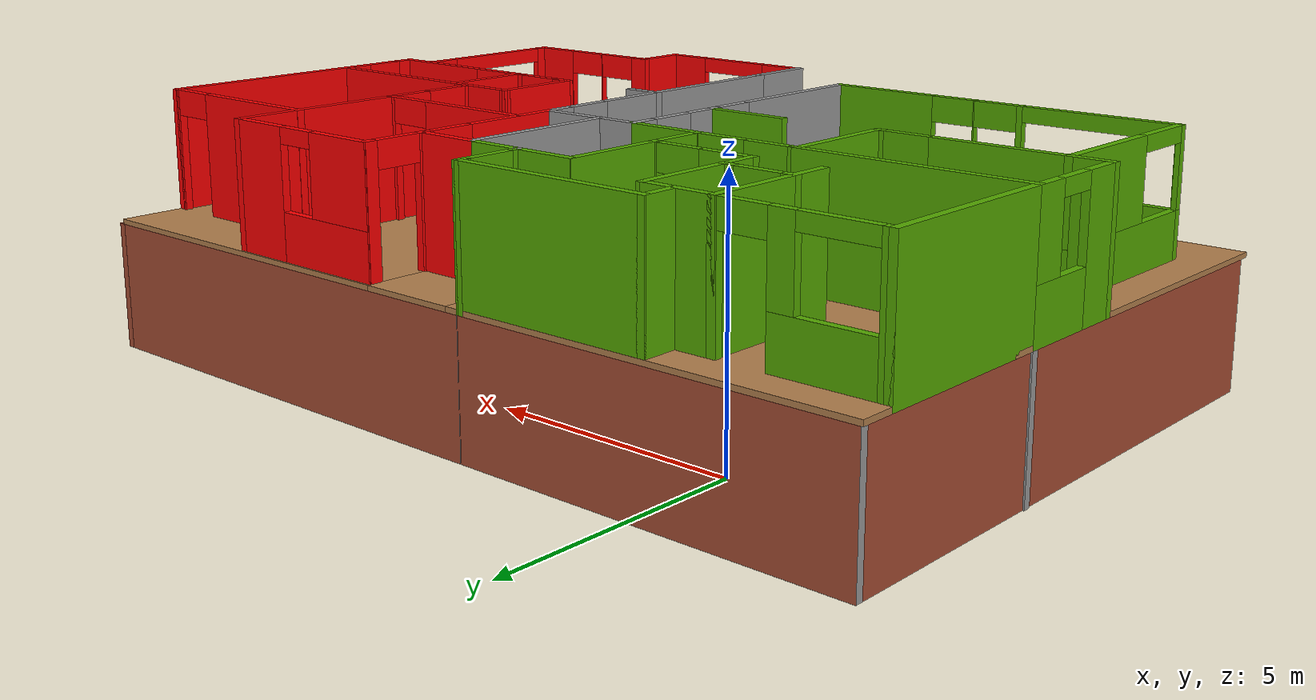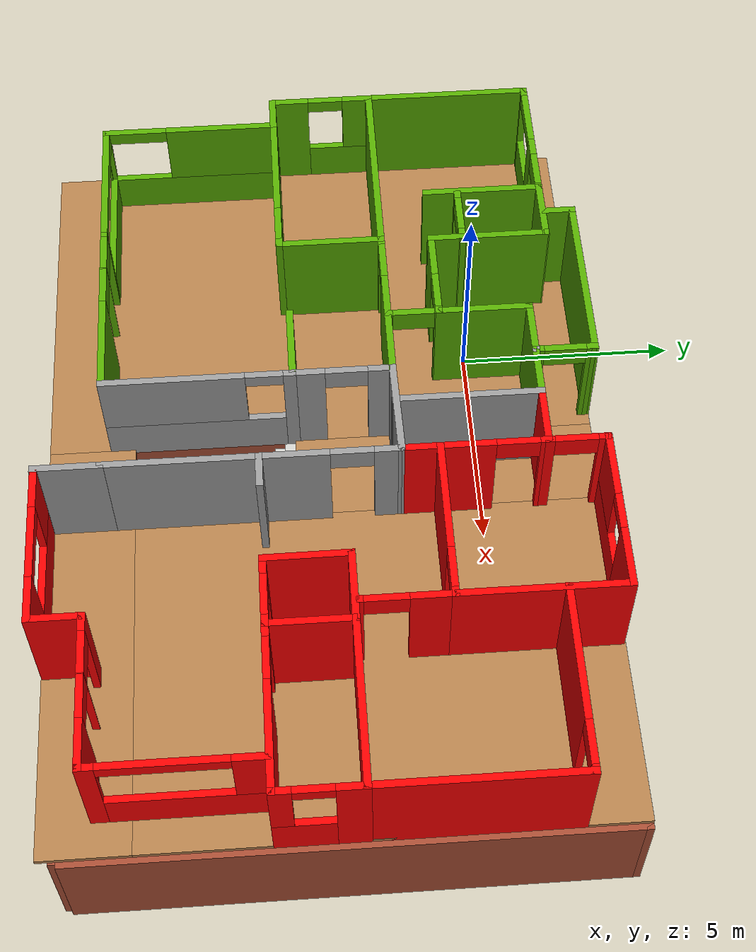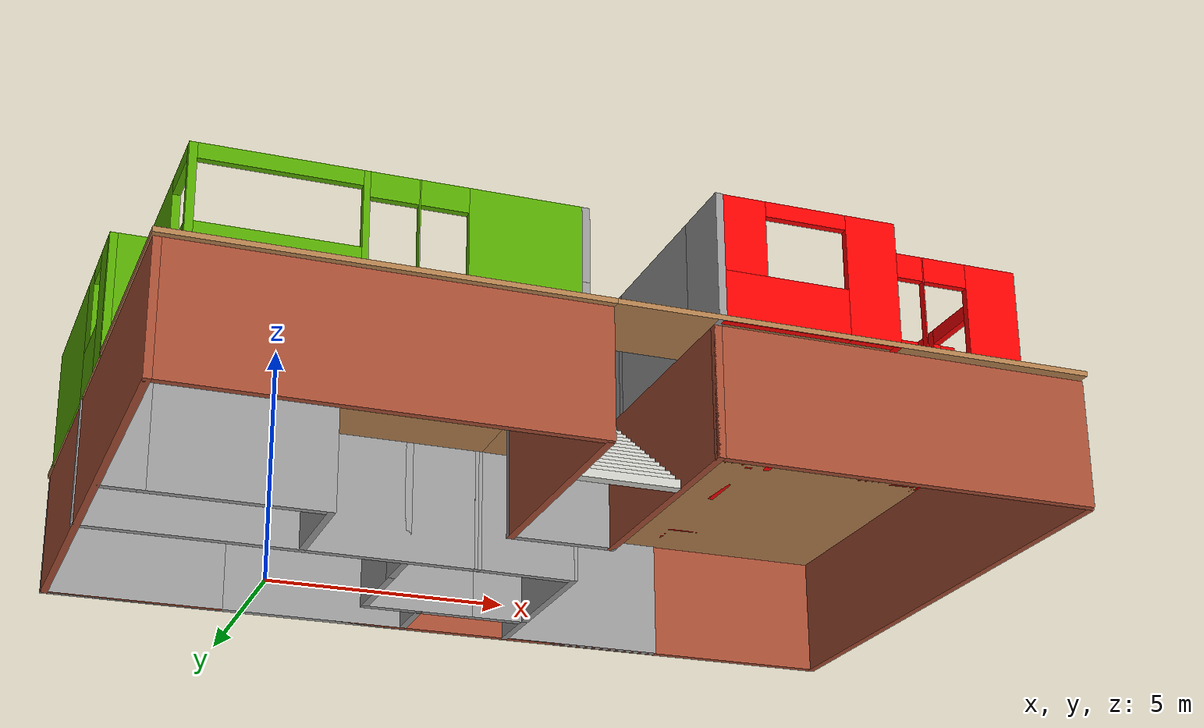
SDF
<?xml version='1.0'?>
<sdf version='1.6'>
  <model name='2floorHouse'>
    <pose frame=''>4.58179 -3.588 0 0 -0 0</pose>
    <link name='Floor_7'>
      <pose frame=''>-0.064 0 2.5 0 -0 0</pose>
      <visual name='Floor_7_Visual_0'>
        <pose frame=''>-4.67984 0 0.05 0 -0 0</pose>
        <geometry>
          <box>
            <size>8.04273 11.89 0.1</size>
          </box>
        </geometry>
        <material>
          <script>
            <uri>file://media/materials/scripts/gazebo.material</uri>
            <name>Gazebo/Wood</name>
          </script>
          <ambient>0 0 1 1</ambient>
        </material>
      </visual>
      <collision name='Floor_7_Collision_0'>
        <geometry>
          <box>
            <size>8.04273 11.89 0.1</size>
          </box>
        </geometry>
        <pose frame=''>-4.67984 0 0.05 0 -0 0</pose>
      </collision>
      <visual name='Floor_7_Visual_1'>
        <pose frame=''>4.02136 -5.01144 0.05 0 -0 0</pose>
        <geometry>
          <box>
            <size>9.35968 1.86713 0.1</size>
          </box>
        </geometry>
        <material>
          <script>
            <uri>file://media/materials/scripts/gazebo.material</uri>
            <name>Gazebo/Wood</name>
          </script>
          <ambient>0 0 1 1</ambient>
        </material>
      </visual>
      <collision name='Floor_7_Collision_1'>
        <geometry>
          <box>
            <size>9.35968 1.86713 0.1</size>
          </box>
        </geometry>
        <pose frame=''>4.02136 -5.01144 0.05 0 -0 0</pose>
      </collision>
      <visual name='Floor_7_Visual_2'>
        <pose frame=''>4.98424 0.933567 0.05 0 -0 0</pose>
        <geometry>
          <box>
            <size>7.43393 10.0229 0.1</size>
          </box>
        </geometry>
        <material>
          <script>
            <uri>file://media/materials/scripts/gazebo.material</uri>
            <name>Gazebo/Wood</name>
          </script>
          <ambient>0 0 1 1</ambient>
        </material>
      </visual>
      <collision name='Floor_7_Collision_2'>
        <geometry>
          <box>
            <size>7.43393 10.0229 0.1</size>
          </box>
        </geometry>
        <pose frame=''>4.98424 0.933567 0.05 0 -0 0</pose>
      </collision>
      <visual name='Floor_7_Visual_3'>
        <pose frame=''>0.304399 2.68357 0.05 0 -0 0</pose>
        <geometry>
          <box>
            <size>1.92575 6.52287 0.1</size>
          </box>
        </geometry>
        <material>
          <script>
            <uri>file://media/materials/scripts/gazebo.material</uri>
            <name>Gazebo/Wood</name>
          </script>
          <ambient>0 0 1 1</ambient>
        </material>
      </visual>
      <collision name='Floor_7_Collision_3'>
        <geometry>
          <box>
            <size>1.92575 6.52287 0.1</size>
          </box>
        </geometry>
        <pose frame=''>0.304399 2.68357 0.05 0 -0 0</pose>
      </collision>
    </link>
    <link name='Stairs_0'>
      <visual name='Stairs_0_Visual_0'>
        <pose frame=''>0.240398 -3.9612 0.083333 0 -0 -3.14159</pose>
        <geometry>
          <box>
            <size>1.92575 0.233333 0.166667</size>
          </box>
        </geometry>
        <material>
          <script>
            <uri>file://media/materials/scripts/gazebo.material</uri>
            <name>Gazebo/CeilingTiled</name>
          </script>
          <ambient>0 0 0 1</ambient>
        </material>
      </visual>
      <collision name='Stairs_0_Collision_0'>
        <geometry>
          <box>
            <size>1.92575 0.233333 0.166667</size>
          </box>
        </geometry>
        <pose frame=''>0.240398 -3.9612 0.083333 0 -0 -3.14159</pose>
      </collision>
      <visual name='Stairs_0_Visual_1'>
        <pose frame=''>0.240398 -3.72787 0.25 0 -0 -3.14159</pose>
        <geometry>
          <box>
            <size>1.92575 0.233333 0.166667</size>
          </box>
        </geometry>
        <material>
          <script>
            <uri>file://media/materials/scripts/gazebo.material</uri>
            <name>Gazebo/CeilingTiled</name>
          </script>
          <ambient>0 0 0 1</ambient>
        </material>
      </visual>
      <collision name='Stairs_0_Collision_1'>
        <geometry>
          <box>
            <size>1.92575 0.233333 0.166667</size>
          </box>
        </geometry>
        <pose frame=''>0.240398 -3.72787 0.25 0 -0 -3.14159</pose>
      </collision>
      <visual name='Stairs_0_Visual_2'>
        <pose frame=''>0.240398 -3.49454 0.416667 0 -0 -3.14159</pose>
        <geometry>
          <box>
            <size>1.92575 0.233333 0.166667</size>
          </box>
        </geometry>
        <material>
          <script>
            <uri>file://media/materials/scripts/gazebo.material</uri>
            <name>Gazebo/CeilingTiled</name>
          </script>
          <ambient>0 0 0 1</ambient>
        </material>
      </visual>
      <collision name='Stairs_0_Collision_2'>
        <geometry>
          <box>
            <size>1.92575 0.233333 0.166667</size>
          </box>
        </geometry>
        <pose frame=''>0.240398 -3.49454 0.416667 0 -0 -3.14159</pose>
      </collision>
      <visual name='Stairs_0_Visual_3'>
        <pose frame=''>0.240398 -3.2612 0.583333 0 -0 -3.14159</pose>
        <geometry>
          <box>
            <size>1.92575 0.233333 0.166667</size>
          </box>
        </geometry>
        <material>
          <script>
            <uri>file://media/materials/scripts/gazebo.material</uri>
            <name>Gazebo/CeilingTiled</name>
          </script>
          <ambient>0 0 0 1</ambient>
        </material>
      </visual>
      <collision name='Stairs_0_Collision_3'>
        <geometry>
          <box>
            <size>1.92575 0.233333 0.166667</size>
          </box>
        </geometry>
        <pose frame=''>0.240398 -3.2612 0.583333 0 -0 -3.14159</pose>
      </collision>
      <visual name='Stairs_0_Visual_4'>
        <pose frame=''>0.240398 -3.02787 0.75 0 -0 -3.14159</pose>
        <geometry>
          <box>
            <size>1.92575 0.233333 0.166667</size>
          </box>
        </geometry>
        <material>
          <script>
            <uri>file://media/materials/scripts/gazebo.material</uri>
            <name>Gazebo/CeilingTiled</name>
          </script>
          <ambient>0 0 0 1</ambient>
        </material>
      </visual>
      <collision name='Stairs_0_Collision_4'>
        <geometry>
          <box>
            <size>1.92575 0.233333 0.166667</size>
          </box>
        </geometry>
        <pose frame=''>0.240398 -3.02787 0.75 0 -0 -3.14159</pose>
      </collision>
      <visual name='Stairs_0_Visual_5'>
        <pose frame=''>0.240398 -2.79454 0.916667 0 -0 -3.14159</pose>
        <geometry>
          <box>
            <size>1.92575 0.233333 0.166667</size>
          </box>
        </geometry>
        <material>
          <script>
            <uri>file://media/materials/scripts/gazebo.material</uri>
            <name>Gazebo/CeilingTiled</name>
          </script>
          <ambient>0 0 0 1</ambient>
        </material>
      </visual>
      <collision name='Stairs_0_Collision_5'>
        <geometry>
          <box>
            <size>1.92575 0.233333 0.166667</size>
          </box>
        </geometry>
        <pose frame=''>0.240398 -2.79454 0.916667 0 -0 -3.14159</pose>
      </collision>
      <visual name='Stairs_0_Visual_6'>
        <pose frame=''>0.240398 -2.5612 1.08333 0 -0 -3.14159</pose>
        <geometry>
          <box>
            <size>1.92575 0.233333 0.166667</size>
          </box>
        </geometry>
        <material>
          <script>
            <uri>file://media/materials/scripts/gazebo.material</uri>
            <name>Gazebo/CeilingTiled</name>
          </script>
          <ambient>0 0 0 1</ambient>
        </material>
      </visual>
      <collision name='Stairs_0_Collision_6'>
        <geometry>
          <box>
            <size>1.92575 0.233333 0.166667</size>
          </box>
        </geometry>
        <pose frame=''>0.240398 -2.5612 1.08333 0 -0 -3.14159</pose>
      </collision>
      <visual name='Stairs_0_Visual_7'>
        <pose frame=''>0.240398 -2.32787 1.25 0 -0 -3.14159</pose>
        <geometry>
          <box>
            <size>1.92575 0.233333 0.166667</size>
          </box>
        </geometry>
        <material>
          <script>
            <uri>file://media/materials/scripts/gazebo.material</uri>
            <name>Gazebo/CeilingTiled</name>
          </script>
          <ambient>0 0 0 1</ambient>
        </material>
      </visual>
      <collision name='Stairs_0_Collision_7'>
        <geometry>
          <box>
            <size>1.92575 0.233333 0.166667</size>
          </box>
        </geometry>
        <pose frame=''>0.240398 -2.32787 1.25 0 -0 -3.14159</pose>
      </collision>
      <visual name='Stairs_0_Visual_8'>
        <pose frame=''>0.240398 -2.09454 1.41667 0 -0 -3.14159</pose>
        <geometry>
          <box>
            <size>1.92575 0.233333 0.166667</size>
          </box>
        </geometry>
        <material>
          <script>
            <uri>file://media/materials/scripts/gazebo.material</uri>
            <name>Gazebo/CeilingTiled</name>
          </script>
          <ambient>0 0 0 1</ambient>
        </material>
      </visual>
      <collision name='Stairs_0_Collision_8'>
        <geometry>
          <box>
            <size>1.92575 0.233333 0.166667</size>
          </box>
        </geometry>
        <pose frame=''>0.240398 -2.09454 1.41667 0 -0 -3.14159</pose>
      </collision>
      <visual name='Stairs_0_Visual_9'>
        <pose frame=''>0.240398 -1.8612 1.58333 0 -0 -3.14159</pose>
        <geometry>
          <box>
            <size>1.92575 0.233333 0.166667</size>
          </box>
        </geometry>
        <material>
          <script>
            <uri>file://media/materials/scripts/gazebo.material</uri>
            <name>Gazebo/CeilingTiled</name>
          </script>
          <ambient>0 0 0 1</ambient>
        </material>
      </visual>
      <collision name='Stairs_0_Collision_9'>
        <geometry>
          <box>
            <size>1.92575 0.233333 0.166667</size>
          </box>
        </geometry>
        <pose frame=''>0.240398 -1.8612 1.58333 0 -0 -3.14159</pose>
      </collision>
      <visual name='Stairs_0_Visual_10'>
        <pose frame=''>0.240398 -1.62787 1.75 0 -0 -3.14159</pose>
        <geometry>
          <box>
            <size>1.92575 0.233333 0.166667</size>
          </box>
        </geometry>
        <material>
          <script>
            <uri>file://media/materials/scripts/gazebo.material</uri>
            <name>Gazebo/CeilingTiled</name>
          </script>
          <ambient>0 0 0 1</ambient>
        </material>
      </visual>
      <collision name='Stairs_0_Collision_10'>
        <geometry>
          <box>
            <size>1.92575 0.233333 0.166667</size>
          </box>
        </geometry>
        <pose frame=''>0.240398 -1.62787 1.75 0 -0 -3.14159</pose>
      </collision>
      <visual name='Stairs_0_Visual_11'>
        <pose frame=''>0.240398 -1.39454 1.91667 0 -0 -3.14159</pose>
        <geometry>
          <box>
            <size>1.92575 0.233333 0.166667</size>
          </box>
        </geometry>
        <material>
          <script>
            <uri>file://media/materials/scripts/gazebo.material</uri>
            <name>Gazebo/CeilingTiled</name>
          </script>
          <ambient>0 0 0 1</ambient>
        </material>
      </visual>
      <collision name='Stairs_0_Collision_11'>
        <geometry>
          <box>
            <size>1.92575 0.233333 0.166667</size>
          </box>
        </geometry>
        <pose frame=''>0.240398 -1.39454 1.91667 0 -0 -3.14159</pose>
      </collision>
      <visual name='Stairs_0_Visual_12'>
        <pose frame=''>0.240398 -1.1612 2.08333 0 -0 -3.14159</pose>
        <geometry>
          <box>
            <size>1.92575 0.233333 0.166667</size>
          </box>
        </geometry>
        <material>
          <script>
            <uri>file://media/materials/scripts/gazebo.material</uri>
            <name>Gazebo/CeilingTiled</name>
          </script>
          <ambient>0 0 0 1</ambient>
        </material>
      </visual>
      <collision name='Stairs_0_Collision_12'>
        <geometry>
          <box>
            <size>1.92575 0.233333 0.166667</size>
          </box>
        </geometry>
        <pose frame=''>0.240398 -1.1612 2.08333 0 -0 -3.14159</pose>
      </collision>
      <visual name='Stairs_0_Visual_13'>
        <pose frame=''>0.240398 -0.92787 2.25 0 -0 -3.14159</pose>
        <geometry>
          <box>
            <size>1.92575 0.233333 0.166667</size>
          </box>
        </geometry>
        <material>
          <script>
            <uri>file://media/materials/scripts/gazebo.material</uri>
            <name>Gazebo/CeilingTiled</name>
          </script>
          <ambient>0 0 0 1</ambient>
        </material>
      </visual>
      <collision name='Stairs_0_Collision_13'>
        <geometry>
          <box>
            <size>1.92575 0.233333 0.166667</size>
          </box>
        </geometry>
        <pose frame=''>0.240398 -0.92787 2.25 0 -0 -3.14159</pose>
      </collision>
      <visual name='Stairs_0_Visual_14'>
        <pose frame=''>0.240398 -0.694536 2.41667 0 -0 -3.14159</pose>
        <geometry>
          <box>
            <size>1.92575 0.233333 0.166667</size>
          </box>
        </geometry>
        <material>
          <script>
            <uri>file://media/materials/scripts/gazebo.material</uri>
            <name>Gazebo/CeilingTiled</name>
          </script>
          <ambient>0 0 0 1</ambient>
        </material>
      </visual>
      <collision name='Stairs_0_Collision_14'>
        <geometry>
          <box>
            <size>1.92575 0.233333 0.166667</size>
          </box>
        </geometry>
        <pose frame=''>0.240398 -0.694536 2.41667 0 -0 -3.14159</pose>
      </collision>
    </link>
    <link name='Wall_100'>
      <collision name='Wall_100_Collision'>
        <geometry>
          <box>
            <size>1.38678 0.15 2.5</size>
          </box>
        </geometry>
        <pose frame=''>0 0 1.25 0 -0 0</pose>
      </collision>
      <visual name='Wall_100_Visual'>
        <pose frame=''>0 0 1.25 0 -0 0</pose>
        <geometry>
          <box>
            <size>1.38678 0.15 2.5</size>
          </box>
        </geometry>
        <material>
          <script>
            <uri>file://media/materials/scripts/gazebo.material</uri>
            <name>Gazebo/Grey</name>
          </script>
          <ambient>1 1 1 1</ambient>
        </material>
      </visual>
      <pose frame=''>0.641704 4.61 0 0 -0 3.14159</pose>
    </link>
    <link name='Wall_106'>
      <collision name='Wall_106_Collision'>
        <geometry>
          <box>
            <size>2.4 0.15 2.5</size>
          </box>
        </geometry>
        <pose frame=''>0 0 1.25 0 -0 0</pose>
      </collision>
      <visual name='Wall_106_Visual'>
        <pose frame=''>0 0 1.25 0 -0 0</pose>
        <geometry>
          <box>
            <size>2.4 0.15 2.5</size>
          </box>
        </geometry>
        <material>
          <script>
            <uri>file://media/materials/scripts/gazebo.material</uri>
            <name>Gazebo/Grey</name>
          </script>
          <ambient>1 1 1 1</ambient>
        </material>
      </visual>
      <pose frame=''>-1.1018 4.61 0 0 -0 3.14159</pose>
    </link>
    <link name='Wall_108'>
      <collision name='Wall_108_Collision'>
        <geometry>
          <box>
            <size>2.1 0.15 2.5</size>
          </box>
        </geometry>
        <pose frame=''>0 0 1.25 0 -0 0</pose>
      </collision>
      <visual name='Wall_108_Visual'>
        <pose frame=''>0 0 1.25 0 -0 0</pose>
        <geometry>
          <box>
            <size>2.1 0.15 2.5</size>
          </box>
        </geometry>
        <material>
          <script>
            <uri>file://media/materials/scripts/gazebo.material</uri>
            <name>Gazebo/Grey</name>
          </script>
          <ambient>1 1 1 1</ambient>
        </material>
      </visual>
      <pose frame=''>-2.23979 3.635 0 0 -0 1.5708</pose>
    </link>
    <link name='Wall_112'>
      <collision name='Wall_112_Collision'>
        <geometry>
          <box>
            <size>4 0.15 2.5</size>
          </box>
        </geometry>
        <pose frame=''>0 0 1.25 0 -0 0</pose>
      </collision>
      <visual name='Wall_112_Visual'>
        <pose frame=''>0 0 1.25 0 -0 0</pose>
        <geometry>
          <box>
            <size>4 0.15 2.5</size>
          </box>
        </geometry>
        <material>
          <script>
            <uri>file://media/materials/scripts/gazebo.material</uri>
            <name>Gazebo/Grey</name>
          </script>
          <ambient>1 1 1 1</ambient>
        </material>
      </visual>
      <pose frame=''>-2.98475 5.8698 0 0 0 -3.14149</pose>
    </link>
    <link name='Wall_115'>
      <collision name='Wall_115_Collision'>
        <geometry>
          <box>
            <size>1.4 0.15 2.5</size>
          </box>
        </geometry>
        <pose frame=''>0 0 1.25 0 -0 0</pose>
      </collision>
      <visual name='Wall_115_Visual'>
        <pose frame=''>0 0 1.25 0 -0 0</pose>
        <geometry>
          <box>
            <size>1.4 0.15 2.5</size>
          </box>
        </geometry>
        <material>
          <script>
            <uri>file://media/materials/scripts/gazebo.material</uri>
            <name>Gazebo/Grey</name>
          </script>
          <ambient>1 1 1 1</ambient>
        </material>
      </visual>
      <pose frame=''>-1.0598 5.245 0 0 0 -1.5708</pose>
    </link>
    <link name='Wall_116'>
      <collision name='Wall_116_Collision'>
        <geometry>
          <box>
            <size>0.15 0.15 2.5</size>
          </box>
        </geometry>
        <pose frame=''>0 0 1.25 0 -0 0</pose>
      </collision>
      <visual name='Wall_116_Visual'>
        <pose frame=''>0 0 1.25 0 -0 0</pose>
        <geometry>
          <box>
            <size>0.15 0.15 2.5</size>
          </box>
        </geometry>
        <material>
          <script>
            <uri>file://media/materials/scripts/gazebo.material</uri>
            <name>Gazebo/Grey</name>
          </script>
          <ambient>1 1 1 1</ambient>
        </material>
      </visual>
      <pose frame=''>-1.0598 4.62 0 0 -0 0</pose>
    </link>
    <link name='Wall_130'>
      <collision name='Wall_130_Collision'>
        <geometry>
          <box>
            <size>3.6 0.15 2.5</size>
          </box>
        </geometry>
        <pose frame=''>0 0 1.25 0 -0 0</pose>
      </collision>
      <visual name='Wall_130_Visual'>
        <pose frame=''>0 0 1.25 0 -0 0</pose>
        <geometry>
          <box>
            <size>3.6 0.15 2.5</size>
          </box>
        </geometry>
        <material>
          <script>
            <uri>file://media/materials/scripts/gazebo.material</uri>
            <name>Gazebo/Grey</name>
          </script>
          <ambient>1 1 1 1</ambient>
        </material>
      </visual>
      <pose frame=''>2.9912 5.838 0 0 -0 3.14159</pose>
    </link>
    <link name='Wall_133'>
      <collision name='Wall_133_Collision'>
        <geometry>
          <box>
            <size>1.35 0.15 2.5</size>
          </box>
        </geometry>
        <pose frame=''>0 0 1.25 0 -0 0</pose>
      </collision>
      <visual name='Wall_133_Visual'>
        <pose frame=''>0 0 1.25 0 -0 0</pose>
        <geometry>
          <box>
            <size>1.35 0.15 2.5</size>
          </box>
        </geometry>
        <material>
          <script>
            <uri>file://media/materials/scripts/gazebo.material</uri>
            <name>Gazebo/Grey</name>
          </script>
          <ambient>1 1 1 1</ambient>
        </material>
      </visual>
      <pose frame=''>1.26021 5.21 0 0 -0 1.5708</pose>
    </link>
    <link name='Wall_292'>
      <pose frame=''>-4.3959 -4.53994 2.5 0 0 -3.14158</pose>
      <visual name='Wall_292_Visual_0'>
        <pose frame=''>-2.52118 0 1.25 0 -0 0</pose>
        <geometry>
          <box>
            <size>2.25743 0.15 2.5</size>
          </box>
        </geometry>
        <material>
          <script>
            <uri>file://media/materials/scripts/gazebo.material</uri>
            <name>Gazebo/Grey</name>
          </script>
          <ambient>0.333333 0.666667 0 1</ambient>
        </material>
      </visual>
      <collision name='Wall_292_Collision_0'>
        <geometry>
          <box>
            <size>2.25743 0.15 2.5</size>
          </box>
        </geometry>
        <pose frame=''>-2.52118 0 1.25 0 -0 0</pose>
      </collision>
      <visual name='Wall_292_Visual_1'>
        <pose frame=''>-0.479853 0 1.25 0 -0 0</pose>
        <geometry>
          <box>
            <size>0.025221 0.15 2.5</size>
          </box>
        </geometry>
        <material>
          <script>
            <uri>file://media/materials/scripts/gazebo.material</uri>
            <name>Gazebo/Grey</name>
          </script>
          <ambient>0.333333 0.666667 0 1</ambient>
        </material>
      </visual>
      <collision name='Wall_292_Collision_1'>
        <geometry>
          <box>
            <size>0.025221 0.15 2.5</size>
          </box>
        </geometry>
        <pose frame=''>-0.479853 0 1.25 0 -0 0</pose>
      </collision>
      <visual name='Wall_292_Visual_2'>
        <pose frame=''>0.492301 0 1.25 0 -0 0</pose>
        <geometry>
          <box>
            <size>0.119086 0.15 2.5</size>
          </box>
        </geometry>
        <material>
          <script>
            <uri>file://media/materials/scripts/gazebo.material</uri>
            <name>Gazebo/Grey</name>
          </script>
          <ambient>0.333333 0.666667 0 1</ambient>
        </material>
      </visual>
      <collision name='Wall_292_Collision_2'>
        <geometry>
          <box>
            <size>0.119086 0.15 2.5</size>
          </box>
        </geometry>
        <pose frame=''>0.492301 0 1.25 0 -0 0</pose>
      </collision>
      <visual name='Wall_292_Visual_3'>
        <pose frame=''>2.10087 0 0.5 0 -0 0</pose>
        <geometry>
          <box>
            <size>3.09805 0.15 1</size>
          </box>
        </geometry>
        <material>
          <script>
            <uri>file://media/materials/scripts/gazebo.material</uri>
            <name>Gazebo/Grey</name>
          </script>
          <ambient>0.333333 0.666667 0 1</ambient>
        </material>
      </visual>
      <collision name='Wall_292_Collision_3'>
        <geometry>
          <box>
            <size>3.09805 0.15 1</size>
          </box>
        </geometry>
        <pose frame=''>2.10087 0 0.5 0 -0 0</pose>
      </collision>
      <visual name='Wall_292_Visual_4'>
        <pose frame=''>3.60087 0 1.75 0 -0 0</pose>
        <geometry>
          <box>
            <size>0.098047 0.15 1.5</size>
          </box>
        </geometry>
        <material>
          <script>
            <uri>file://media/materials/scripts/gazebo.material</uri>
            <name>Gazebo/Grey</name>
          </script>
          <ambient>0.333333 0.666667 0 1</ambient>
        </material>
      </visual>
      <collision name='Wall_292_Collision_4'>
        <geometry>
          <box>
            <size>0.098047 0.15 1.5</size>
          </box>
        </geometry>
        <pose frame=''>3.60087 0 1.75 0 -0 0</pose>
      </collision>
      <visual name='Wall_292_Visual_5'>
        <pose frame=''>-0.942463 0 2.25 0 -0 0</pose>
        <geometry>
          <box>
            <size>0.9 0.15 0.5</size>
          </box>
        </geometry>
        <material>
          <script>
            <uri>file://media/materials/scripts/gazebo.material</uri>
            <name>Gazebo/Grey</name>
          </script>
          <ambient>0.333333 0.666667 0 1</ambient>
        </material>
      </visual>
      <collision name='Wall_292_Collision_5'>
        <geometry>
          <box>
            <size>0.9 0.15 0.5</size>
          </box>
        </geometry>
        <pose frame=''>-0.942463 0 2.25 0 -0 0</pose>
      </collision>
      <visual name='Wall_292_Visual_6'>
        <pose frame=''>-0.017242 0 2.25 0 -0 0</pose>
        <geometry>
          <box>
            <size>0.9 0.15 0.5</size>
          </box>
        </geometry>
        <material>
          <script>
            <uri>file://media/materials/scripts/gazebo.material</uri>
            <name>Gazebo/Grey</name>
          </script>
          <ambient>0.333333 0.666667 0 1</ambient>
        </material>
      </visual>
      <collision name='Wall_292_Collision_6'>
        <geometry>
          <box>
            <size>0.9 0.15 0.5</size>
          </box>
        </geometry>
        <pose frame=''>-0.017242 0 2.25 0 -0 0</pose>
      </collision>
      <visual name='Wall_292_Visual_7'>
        <pose frame=''>2.05184 0 2.35 0 -0 0</pose>
        <geometry>
          <box>
            <size>3 0.15 0.3</size>
          </box>
        </geometry>
        <material>
          <script>
            <uri>file://media/materials/scripts/gazebo.material</uri>
            <name>Gazebo/Grey</name>
          </script>
          <ambient>0.333333 0.666667 0 1</ambient>
        </material>
      </visual>
      <collision name='Wall_292_Collision_7'>
        <geometry>
          <box>
            <size>3 0.15 0.3</size>
          </box>
        </geometry>
        <pose frame=''>2.05184 0 2.35 0 -0 0</pose>
      </collision>
    </link>
    <link name='Wall_293'>
      <pose frame=''>-7.97079 -2.615 2.5 0 -0 1.5708</pose>
      <visual name='Wall_293_Visual_0'>
        <pose frame=''>-1.97712 0 1.25 0 -0 0</pose>
        <geometry>
          <box>
            <size>0.045764 0.15 2.5</size>
          </box>
        </geometry>
        <material>
          <script>
            <uri>file://media/materials/scripts/gazebo.material</uri>
            <name>Gazebo/Grey</name>
          </script>
          <ambient>0.333333 0.666667 0 1</ambient>
        </material>
      </visual>
      <collision name='Wall_293_Collision_0'>
        <geometry>
          <box>
            <size>0.045764 0.15 2.5</size>
          </box>
        </geometry>
        <pose frame=''>-1.97712 0 1.25 0 -0 0</pose>
      </collision>
      <visual name='Wall_293_Visual_1'>
        <pose frame=''>0.022882 0 0.5 0 -0 0</pose>
        <geometry>
          <box>
            <size>3.95424 0.15 1</size>
          </box>
        </geometry>
        <material>
          <script>
            <uri>file://media/materials/scripts/gazebo.material</uri>
            <name>Gazebo/Grey</name>
          </script>
          <ambient>0.333333 0.666667 0 1</ambient>
        </material>
      </visual>
      <collision name='Wall_293_Collision_1'>
        <geometry>
          <box>
            <size>3.95424 0.15 1</size>
          </box>
        </geometry>
        <pose frame=''>0.022882 0 0.5 0 -0 0</pose>
      </collision>
      <visual name='Wall_293_Visual_2'>
        <pose frame=''>0.722882 0 1.75 0 -0 0</pose>
        <geometry>
          <box>
            <size>2.55424 0.15 1.5</size>
          </box>
        </geometry>
        <material>
          <script>
            <uri>file://media/materials/scripts/gazebo.material</uri>
            <name>Gazebo/Grey</name>
          </script>
          <ambient>0.333333 0.666667 0 1</ambient>
        </material>
      </visual>
      <collision name='Wall_293_Collision_2'>
        <geometry>
          <box>
            <size>2.55424 0.15 1.5</size>
          </box>
        </geometry>
        <pose frame=''>0.722882 0 1.75 0 -0 0</pose>
      </collision>
      <visual name='Wall_293_Visual_3'>
        <pose frame=''>-1.25424 0 2.35 0 -0 0</pose>
        <geometry>
          <box>
            <size>1.4 0.15 0.3</size>
          </box>
        </geometry>
        <material>
          <script>
            <uri>file://media/materials/scripts/gazebo.material</uri>
            <name>Gazebo/Grey</name>
          </script>
          <ambient>0.333333 0.666667 0 1</ambient>
        </material>
      </visual>
      <collision name='Wall_293_Collision_3'>
        <geometry>
          <box>
            <size>1.4 0.15 0.3</size>
          </box>
        </geometry>
        <pose frame=''>-1.25424 0 2.35 0 -0 0</pose>
      </collision>
    </link>
    <link name='Wall_294'>
      <collision name='Wall_294_Collision'>
        <geometry>
          <box>
            <size>0.86941 0.15 2.5</size>
          </box>
        </geometry>
        <pose frame=''>0 0 1.25 0 -0 0</pose>
      </collision>
      <visual name='Wall_294_Visual'>
        <pose frame=''>0 0 1.25 0 -0 0</pose>
        <geometry>
          <box>
            <size>0.86941 0.15 2.5</size>
          </box>
        </geometry>
        <material>
          <script>
            <uri>file://media/materials/scripts/gazebo.material</uri>
            <name>Gazebo/Grey</name>
          </script>
          <ambient>0.333333 0.666667 0 1</ambient>
        </material>
      </visual>
      <pose frame=''>-8.3305 -0.690004 2.5 0 -0 3.14159</pose>
    </link>
    <link name='Wall_295'>
      <pose frame=''>-8.69021 0.434996 2.5 0 -0 1.5708</pose>
      <visual name='Wall_295_Visual_0'>
        <pose frame=''>-0.748437 0 1.25 0 -0 0</pose>
        <geometry>
          <box>
            <size>0.903127 0.15 2.5</size>
          </box>
        </geometry>
        <material>
          <script>
            <uri>file://media/materials/scripts/gazebo.material</uri>
            <name>Gazebo/Grey</name>
          </script>
          <ambient>0.333333 0.666667 0 1</ambient>
        </material>
      </visual>
      <collision name='Wall_295_Collision_0'>
        <geometry>
          <box>
            <size>0.903127 0.15 2.5</size>
          </box>
        </geometry>
        <pose frame=''>-0.748437 0 1.25 0 -0 0</pose>
      </collision>
      <visual name='Wall_295_Visual_1'>
        <pose frame=''>0.451563 0 0.5 0 -0 0</pose>
        <geometry>
          <box>
            <size>1.49687 0.15 1</size>
          </box>
        </geometry>
        <material>
          <script>
            <uri>file://media/materials/scripts/gazebo.material</uri>
            <name>Gazebo/Grey</name>
          </script>
          <ambient>0.333333 0.666667 0 1</ambient>
        </material>
      </visual>
      <collision name='Wall_295_Collision_1'>
        <geometry>
          <box>
            <size>1.49687 0.15 1</size>
          </box>
        </geometry>
        <pose frame=''>0.451563 0 0.5 0 -0 0</pose>
      </collision>
      <visual name='Wall_295_Visual_2'>
        <pose frame=''>0.851563 0 1.75 0 -0 0</pose>
        <geometry>
          <box>
            <size>0.696873 0.15 1.5</size>
          </box>
        </geometry>
        <material>
          <script>
            <uri>file://media/materials/scripts/gazebo.material</uri>
            <name>Gazebo/Grey</name>
          </script>
          <ambient>0.333333 0.666667 0 1</ambient>
        </material>
      </visual>
      <collision name='Wall_295_Collision_2'>
        <geometry>
          <box>
            <size>0.696873 0.15 1.5</size>
          </box>
        </geometry>
        <pose frame=''>0.851563 0 1.75 0 -0 0</pose>
      </collision>
      <visual name='Wall_295_Visual_3'>
        <pose frame=''>0.103127 0 2.35 0 -0 0</pose>
        <geometry>
          <box>
            <size>0.8 0.15 0.3</size>
          </box>
        </geometry>
        <material>
          <script>
            <uri>file://media/materials/scripts/gazebo.material</uri>
            <name>Gazebo/Grey</name>
          </script>
          <ambient>0.333333 0.666667 0 1</ambient>
        </material>
      </visual>
      <collision name='Wall_295_Collision_3'>
        <geometry>
          <box>
            <size>0.8 0.15 0.3</size>
          </box>
        </geometry>
        <pose frame=''>0.103127 0 2.35 0 -0 0</pose>
      </collision>
    </link>
    <link name='Wall_296'>
      <collision name='Wall_296_Collision'>
        <geometry>
          <box>
            <size>4.5 0.15 2.5</size>
          </box>
        </geometry>
        <pose frame=''>0 0 1.25 0 -0 0</pose>
      </collision>
      <visual name='Wall_296_Visual'>
        <pose frame=''>0 0 1.25 0 -0 0</pose>
        <geometry>
          <box>
            <size>4.5 0.15 2.5</size>
          </box>
        </geometry>
        <material>
          <script>
            <uri>file://media/materials/scripts/gazebo.material</uri>
            <name>Gazebo/Grey</name>
          </script>
          <ambient>0.333333 0.666667 0 1</ambient>
        </material>
      </visual>
      <pose frame=''>-6.5152 1.56 2.5 0 -0 0</pose>
    </link>
    <link name='Wall_297'>
      <collision name='Wall_297_Collision'>
        <geometry>
          <box>
            <size>2.4 0.15 2.5</size>
          </box>
        </geometry>
        <pose frame=''>0 0 1.25 0 -0 0</pose>
      </collision>
      <visual name='Wall_297_Visual'>
        <pose frame=''>0 0 1.25 0 -0 0</pose>
        <geometry>
          <box>
            <size>2.4 0.15 2.5</size>
          </box>
        </geometry>
        <material>
          <script>
            <uri>file://media/materials/scripts/gazebo.material</uri>
            <name>Gazebo/Grey</name>
          </script>
          <ambient>0.333333 0.666667 0 1</ambient>
        </material>
      </visual>
      <pose frame=''>-4.34021 0.434996 2.5 0 0 -1.5708</pose>
    </link>
    <link name='Wall_298'>
      <pose frame=''>-6.1555 -0.690004 2.5 0 -0 3.14159</pose>
      <visual name='Wall_298_Visual_0'>
        <pose frame=''>-1.77022 0 1.25 0 -0 0</pose>
        <geometry>
          <box>
            <size>0.240159 0.15 2.5</size>
          </box>
        </geometry>
        <material>
          <script>
            <uri>file://media/materials/scripts/gazebo.material</uri>
            <name>Gazebo/Grey</name>
          </script>
          <ambient>0.333333 0.666667 0 1</ambient>
        </material>
      </visual>
      <collision name='Wall_298_Collision_0'>
        <geometry>
          <box>
            <size>0.240159 0.15 2.5</size>
          </box>
        </geometry>
        <pose frame=''>-1.77022 0 1.25 0 -0 0</pose>
      </collision>
      <visual name='Wall_298_Visual_1'>
        <pose frame=''>0.570079 0 1.25 0 -0 0</pose>
        <geometry>
          <box>
            <size>2.64043 0.15 2.5</size>
          </box>
        </geometry>
        <material>
          <script>
            <uri>file://media/materials/scripts/gazebo.material</uri>
            <name>Gazebo/Grey</name>
          </script>
          <ambient>0.333333 0.666667 0 1</ambient>
        </material>
      </visual>
      <collision name='Wall_298_Collision_1'>
        <geometry>
          <box>
            <size>2.64043 0.15 2.5</size>
          </box>
        </geometry>
        <pose frame=''>0.570079 0 1.25 0 -0 0</pose>
      </collision>
      <visual name='Wall_298_Visual_2'>
        <pose frame=''>-1.20014 0 2.25 0 -0 0</pose>
        <geometry>
          <box>
            <size>0.9 0.15 0.5</size>
          </box>
        </geometry>
        <material>
          <script>
            <uri>file://media/materials/scripts/gazebo.material</uri>
            <name>Gazebo/Grey</name>
          </script>
          <ambient>0.333333 0.666667 0 1</ambient>
        </material>
      </visual>
      <collision name='Wall_298_Collision_2'>
        <geometry>
          <box>
            <size>0.9 0.15 0.5</size>
          </box>
        </geometry>
        <pose frame=''>-1.20014 0 2.25 0 -0 0</pose>
      </collision>
    </link>
    <link name='Wall_299'>
      <pose frame=''>-2.565 1.56 2.5 0 -0 0</pose>
      <visual name='Wall_299_Visual_0'>
        <pose frame=''>-1.73627 0 1.25 0 -0 0</pose>
        <geometry>
          <box>
            <size>0.227865 0.15 2.5</size>
          </box>
        </geometry>
        <material>
          <script>
            <uri>file://media/materials/scripts/gazebo.material</uri>
            <name>Gazebo/Grey</name>
          </script>
          <ambient>0.333333 0.666667 0 1</ambient>
        </material>
      </visual>
      <collision name='Wall_299_Collision_0'>
        <geometry>
          <box>
            <size>0.227865 0.15 2.5</size>
          </box>
        </geometry>
        <pose frame=''>-1.73627 0 1.25 0 -0 0</pose>
      </collision>
      <visual name='Wall_299_Visual_1'>
        <pose frame=''>0.563933 0 1.25 0 -0 0</pose>
        <geometry>
          <box>
            <size>2.57254 0.15 2.5</size>
          </box>
        </geometry>
        <material>
          <script>
            <uri>file://media/materials/scripts/gazebo.material</uri>
            <name>Gazebo/Grey</name>
          </script>
          <ambient>0.333333 0.666667 0 1</ambient>
        </material>
      </visual>
      <collision name='Wall_299_Collision_1'>
        <geometry>
          <box>
            <size>2.57254 0.15 2.5</size>
          </box>
        </geometry>
        <pose frame=''>0.563933 0 1.25 0 -0 0</pose>
      </collision>
      <visual name='Wall_299_Visual_2'>
        <pose frame=''>-1.17234 0 2.25 0 -0 0</pose>
        <geometry>
          <box>
            <size>0.9 0.15 0.5</size>
          </box>
        </geometry>
        <material>
          <script>
            <uri>file://media/materials/scripts/gazebo.material</uri>
            <name>Gazebo/Grey</name>
          </script>
          <ambient>0.333333 0.666667 0 1</ambient>
        </material>
      </visual>
      <collision name='Wall_299_Collision_2'>
        <geometry>
          <box>
            <size>0.9 0.15 0.5</size>
          </box>
        </geometry>
        <pose frame=''>-1.17234 0 2.25 0 -0 0</pose>
      </collision>
    </link>
    <link name='Wall_300'>
      <pose frame=''>-0.789795 0.509996 2.5 0 0 -1.5708</pose>
      <visual name='Wall_300_Visual_0'>
        <pose frame=''>-0.8265 0 1.25 0 -0 0</pose>
        <geometry>
          <box>
            <size>0.597 0.15 2.5</size>
          </box>
        </geometry>
        <material>
          <script>
            <uri>file://media/materials/scripts/gazebo.material</uri>
            <name>Gazebo/Grey</name>
          </script>
          <ambient>1 1 1 1</ambient>
        </material>
      </visual>
      <collision name='Wall_300_Collision_0'>
        <geometry>
          <box>
            <size>0.597 0.15 2.5</size>
          </box>
        </geometry>
        <pose frame=''>-0.8265 0 1.25 0 -0 0</pose>
      </collision>
      <visual name='Wall_300_Visual_1'>
        <pose frame=''>0.7485 0 1.25 0 -0 0</pose>
        <geometry>
          <box>
            <size>0.753 0.15 2.5</size>
          </box>
        </geometry>
        <material>
          <script>
            <uri>file://media/materials/scripts/gazebo.material</uri>
            <name>Gazebo/Grey</name>
          </script>
          <ambient>1 1 1 1</ambient>
        </material>
      </visual>
      <collision name='Wall_300_Collision_1'>
        <geometry>
          <box>
            <size>0.753 0.15 2.5</size>
          </box>
        </geometry>
        <pose frame=''>0.7485 0 1.25 0 -0 0</pose>
      </collision>
      <visual name='Wall_300_Visual_2'>
        <pose frame=''>-0.078 0 2.25 0 -0 0</pose>
        <geometry>
          <box>
            <size>0.9 0.15 0.5</size>
          </box>
        </geometry>
        <material>
          <script>
            <uri>file://media/materials/scripts/gazebo.material</uri>
            <name>Gazebo/Grey</name>
          </script>
          <ambient>1 1 1 1</ambient>
        </material>
      </visual>
      <collision name='Wall_300_Collision_2'>
        <geometry>
          <box>
            <size>0.9 0.15 0.5</size>
          </box>
        </geometry>
        <pose frame=''>-0.078 0 2.25 0 -0 0</pose>
      </collision>
    </link>
    <link name='Wall_301'>
      <collision name='Wall_301_Collision'>
        <geometry>
          <box>
            <size>1.75 0.15 2.5</size>
          </box>
        </geometry>
        <pose frame=''>0 0 1.25 0 -0 0</pose>
      </collision>
      <visual name='Wall_301_Visual'>
        <pose frame=''>0 0 1.25 0 -0 0</pose>
        <geometry>
          <box>
            <size>1.75 0.15 2.5</size>
          </box>
        </geometry>
        <material>
          <script>
            <uri>file://media/materials/scripts/gazebo.material</uri>
            <name>Gazebo/Grey</name>
          </script>
          <ambient>0.333333 0.666667 0 1</ambient>
        </material>
      </visual>
      <pose frame=''>-1.5898 -0.540004 2.5 0 -0 3.14159</pose>
    </link>
    <link name='Wall_302'>
      <pose frame=''>-0.789795 -2.54 2.5 0 0 -1.5708</pose>
      <visual name='Wall_302_Visual_0'>
        <pose frame=''>-1.93765 0 1.25 0 -0 0</pose>
        <geometry>
          <box>
            <size>0.274706 0.15 2.5</size>
          </box>
        </geometry>
        <material>
          <script>
            <uri>file://media/materials/scripts/gazebo.material</uri>
            <name>Gazebo/Grey</name>
          </script>
          <ambient>1 1 1 1</ambient>
        </material>
      </visual>
      <collision name='Wall_302_Collision_0'>
        <geometry>
          <box>
            <size>0.274706 0.15 2.5</size>
          </box>
        </geometry>
        <pose frame=''>-1.93765 0 1.25 0 -0 0</pose>
      </collision>
      <visual name='Wall_302_Visual_1'>
        <pose frame=''>0.137353 0 0.5 0 -0 0</pose>
        <geometry>
          <box>
            <size>3.87529 0.15 1</size>
          </box>
        </geometry>
        <material>
          <script>
            <uri>file://media/materials/scripts/gazebo.material</uri>
            <name>Gazebo/Grey</name>
          </script>
          <ambient>1 1 1 1</ambient>
        </material>
      </visual>
      <collision name='Wall_302_Collision_1'>
        <geometry>
          <box>
            <size>3.87529 0.15 1</size>
          </box>
        </geometry>
        <pose frame=''>0.137353 0 0.5 0 -0 0</pose>
      </collision>
      <visual name='Wall_302_Visual_2'>
        <pose frame=''>0.537353 0 1.75 0 -0 0</pose>
        <geometry>
          <box>
            <size>3.07529 0.15 1.5</size>
          </box>
        </geometry>
        <material>
          <script>
            <uri>file://media/materials/scripts/gazebo.material</uri>
            <name>Gazebo/Grey</name>
          </script>
          <ambient>1 1 1 1</ambient>
        </material>
      </visual>
      <collision name='Wall_302_Collision_2'>
        <geometry>
          <box>
            <size>3.07529 0.15 1.5</size>
          </box>
        </geometry>
        <pose frame=''>0.537353 0 1.75 0 -0 0</pose>
      </collision>
      <visual name='Wall_302_Visual_3'>
        <pose frame=''>-1.40029 0 2.35 0 -0 0</pose>
        <geometry>
          <box>
            <size>0.8 0.15 0.3</size>
          </box>
        </geometry>
        <material>
          <script>
            <uri>file://media/materials/scripts/gazebo.material</uri>
            <name>Gazebo/Grey</name>
          </script>
          <ambient>1 1 1 1</ambient>
        </material>
      </visual>
      <collision name='Wall_302_Collision_3'>
        <geometry>
          <box>
            <size>0.8 0.15 0.3</size>
          </box>
        </geometry>
        <pose frame=''>-1.40029 0 2.35 0 -0 0</pose>
      </collision>
    </link>
    <link name='Wall_303'>
      <collision name='Wall_303_Collision'>
        <geometry>
          <box>
            <size>3.8 0.15 2.5</size>
          </box>
        </geometry>
        <pose frame=''>0 0 1.25 0 -0 0</pose>
      </collision>
      <visual name='Wall_303_Visual'>
        <pose frame=''>0 0 1.25 0 -0 0</pose>
        <geometry>
          <box>
            <size>3.8 0.15 2.5</size>
          </box>
        </geometry>
        <material>
          <script>
            <uri>file://media/materials/scripts/gazebo.material</uri>
            <name>Gazebo/Grey</name>
          </script>
          <ambient>0.333333 0.666667 0 1</ambient>
        </material>
      </visual>
      <pose frame=''>-8.69021 3.385 2.5 0 -0 1.5708</pose>
    </link>
    <link name='Wall_304'>
      <pose frame=''>-7.16521 5.21 2.5 0 -0 0</pose>
      <visual name='Wall_304_Visual_0'>
        <pose frame=''>-1.47576 0 1.25 0 -0 0</pose>
        <geometry>
          <box>
            <size>0.248475 0.15 2.5</size>
          </box>
        </geometry>
        <material>
          <script>
            <uri>file://media/materials/scripts/gazebo.material</uri>
            <name>Gazebo/Grey</name>
          </script>
          <ambient>0.333333 0.666667 0 1</ambient>
        </material>
      </visual>
      <collision name='Wall_304_Collision_0'>
        <geometry>
          <box>
            <size>0.248475 0.15 2.5</size>
          </box>
        </geometry>
        <pose frame=''>-1.47576 0 1.25 0 -0 0</pose>
      </collision>
      <visual name='Wall_304_Visual_1'>
        <pose frame=''>1.51114 0 1.25 0 -0 0</pose>
        <geometry>
          <box>
            <size>0.177722 0.15 2.5</size>
          </box>
        </geometry>
        <material>
          <script>
            <uri>file://media/materials/scripts/gazebo.material</uri>
            <name>Gazebo/Grey</name>
          </script>
          <ambient>0.333333 0.666667 0 1</ambient>
        </material>
      </visual>
      <collision name='Wall_304_Collision_1'>
        <geometry>
          <box>
            <size>0.177722 0.15 2.5</size>
          </box>
        </geometry>
        <pose frame=''>1.51114 0 1.25 0 -0 0</pose>
      </collision>
      <visual name='Wall_304_Visual_2'>
        <pose frame=''>-0.414623 0 0.5 0 -0 0</pose>
        <geometry>
          <box>
            <size>1.8738 0.15 1</size>
          </box>
        </geometry>
        <material>
          <script>
            <uri>file://media/materials/scripts/gazebo.material</uri>
            <name>Gazebo/Grey</name>
          </script>
          <ambient>0.333333 0.666667 0 1</ambient>
        </material>
      </visual>
      <collision name='Wall_304_Collision_2'>
        <geometry>
          <box>
            <size>1.8738 0.15 1</size>
          </box>
        </geometry>
        <pose frame=''>-0.414623 0 0.5 0 -0 0</pose>
      </collision>
      <visual name='Wall_304_Visual_3'>
        <pose frame=''>0.285377 0 1.75 0 -0 0</pose>
        <geometry>
          <box>
            <size>0.473803 0.15 1.5</size>
          </box>
        </geometry>
        <material>
          <script>
            <uri>file://media/materials/scripts/gazebo.material</uri>
            <name>Gazebo/Grey</name>
          </script>
          <ambient>0.333333 0.666667 0 1</ambient>
        </material>
      </visual>
      <collision name='Wall_304_Collision_3'>
        <geometry>
          <box>
            <size>0.473803 0.15 1.5</size>
          </box>
        </geometry>
        <pose frame=''>0.285377 0 1.75 0 -0 0</pose>
      </collision>
      <visual name='Wall_304_Visual_4'>
        <pose frame=''>0.972278 0 2.25 0 -0 0</pose>
        <geometry>
          <box>
            <size>0.9 0.15 0.5</size>
          </box>
        </geometry>
        <material>
          <script>
            <uri>file://media/materials/scripts/gazebo.material</uri>
            <name>Gazebo/Grey</name>
          </script>
          <ambient>0.333333 0.666667 0 1</ambient>
        </material>
      </visual>
      <collision name='Wall_304_Collision_4'>
        <geometry>
          <box>
            <size>0.9 0.15 0.5</size>
          </box>
        </geometry>
        <pose frame=''>0.972278 0 2.25 0 -0 0</pose>
      </collision>
      <visual name='Wall_304_Visual_5'>
        <pose frame=''>-0.651525 0 2.35 0 -0 0</pose>
        <geometry>
          <box>
            <size>1.4 0.15 0.3</size>
          </box>
        </geometry>
        <material>
          <script>
            <uri>file://media/materials/scripts/gazebo.material</uri>
            <name>Gazebo/Grey</name>
          </script>
          <ambient>0.333333 0.666667 0 1</ambient>
        </material>
      </visual>
      <collision name='Wall_304_Collision_5'>
        <geometry>
          <box>
            <size>1.4 0.15 0.3</size>
          </box>
        </geometry>
        <pose frame=''>-0.651525 0 2.35 0 -0 0</pose>
      </collision>
    </link>
    <link name='Wall_305'>
      <collision name='Wall_305_Collision'>
        <geometry>
          <box>
            <size>2.7 0.15 2.5</size>
          </box>
        </geometry>
        <pose frame=''>0 0 1.25 0 -0 0</pose>
      </collision>
      <visual name='Wall_305_Visual'>
        <pose frame=''>0 0 1.25 0 -0 0</pose>
        <geometry>
          <box>
            <size>2.7 0.15 2.5</size>
          </box>
        </geometry>
        <material>
          <script>
            <uri>file://media/materials/scripts/gazebo.material</uri>
            <name>Gazebo/Grey</name>
          </script>
          <ambient>0.333333 0.666667 0 1</ambient>
        </material>
      </visual>
      <pose frame=''>-5.6402 3.935 2.5 0 0 -1.5708</pose>
    </link>
    <link name='Wall_306'>
      <collision name='Wall_306_Collision'>
        <geometry>
          <box>
            <size>1.5 0.15 2.5</size>
          </box>
        </geometry>
        <pose frame=''>0 0 1.25 0 -0 0</pose>
      </collision>
      <visual name='Wall_306_Visual'>
        <pose frame=''>0 0 1.25 0 -0 0</pose>
        <geometry>
          <box>
            <size>1.5 0.15 2.5</size>
          </box>
        </geometry>
        <material>
          <script>
            <uri>file://media/materials/scripts/gazebo.material</uri>
            <name>Gazebo/Grey</name>
          </script>
          <ambient>0.333333 0.666667 0 1</ambient>
        </material>
      </visual>
      <pose frame=''>-4.96521 5.21 2.5 0 -0 0</pose>
    </link>
    <link name='Wall_307'>
      <collision name='Wall_307_Collision'>
        <geometry>
          <box>
            <size>2 0.15 2.5</size>
          </box>
        </geometry>
        <pose frame=''>0 0 1.25 0 -0 0</pose>
      </collision>
      <visual name='Wall_307_Visual'>
        <pose frame=''>0 0 1.25 0 -0 0</pose>
        <geometry>
          <box>
            <size>2 0.15 2.5</size>
          </box>
        </geometry>
        <material>
          <script>
            <uri>file://media/materials/scripts/gazebo.material</uri>
            <name>Gazebo/Grey</name>
          </script>
          <ambient>0.333333 0.666667 0 1</ambient>
        </material>
      </visual>
      <pose frame=''>-4.29 4.285 2.5 0 0 -1.57058</pose>
    </link>
    <link name='Wall_308'>
      <pose frame=''>-4.965 3.36 2.5 0 -0 3.14159</pose>
      <visual name='Wall_308_Visual_0'>
        <pose frame=''>-0.593035 0 1.25 0 -0 0</pose>
        <geometry>
          <box>
            <size>0.314339 0.15 2.5</size>
          </box>
        </geometry>
        <material>
          <script>
            <uri>file://media/materials/scripts/gazebo.material</uri>
            <name>Gazebo/Grey</name>
          </script>
          <ambient>0.333333 0.666667 0 1</ambient>
        </material>
      </visual>
      <collision name='Wall_308_Collision_0'>
        <geometry>
          <box>
            <size>0.314339 0.15 2.5</size>
          </box>
        </geometry>
        <pose frame=''>-0.593035 0 1.25 0 -0 0</pose>
      </collision>
      <visual name='Wall_308_Visual_1'>
        <pose frame=''>0.607169 0 1.25 0 -0 0</pose>
        <geometry>
          <box>
            <size>0.286071 0.15 2.5</size>
          </box>
        </geometry>
        <material>
          <script>
            <uri>file://media/materials/scripts/gazebo.material</uri>
            <name>Gazebo/Grey</name>
          </script>
          <ambient>0.333333 0.666667 0 1</ambient>
        </material>
      </visual>
      <collision name='Wall_308_Collision_1'>
        <geometry>
          <box>
            <size>0.286071 0.15 2.5</size>
          </box>
        </geometry>
        <pose frame=''>0.607169 0 1.25 0 -0 0</pose>
      </collision>
      <visual name='Wall_308_Visual_2'>
        <pose frame=''>0.014134 0 2.25 0 -0 0</pose>
        <geometry>
          <box>
            <size>0.9 0.15 0.5</size>
          </box>
        </geometry>
        <material>
          <script>
            <uri>file://media/materials/scripts/gazebo.material</uri>
            <name>Gazebo/Grey</name>
          </script>
          <ambient>0.333333 0.666667 0 1</ambient>
        </material>
      </visual>
      <collision name='Wall_308_Collision_2'>
        <geometry>
          <box>
            <size>0.9 0.15 0.5</size>
          </box>
        </geometry>
        <pose frame=''>0.014134 0 2.25 0 -0 0</pose>
      </collision>
    </link>
    <link name='Wall_309'>
      <collision name='Wall_309_Collision'>
        <geometry>
          <box>
            <size>0.85 0.15 2.5</size>
          </box>
        </geometry>
        <pose frame=''>0 0 1.25 0 -0 0</pose>
      </collision>
      <visual name='Wall_309_Visual'>
        <pose frame=''>0 0 1.25 0 -0 0</pose>
        <geometry>
          <box>
            <size>0.85 0.15 2.5</size>
          </box>
        </geometry>
        <material>
          <script>
            <uri>file://media/materials/scripts/gazebo.material</uri>
            <name>Gazebo/Grey</name>
          </script>
          <ambient>0.333333 0.666667 0 1</ambient>
        </material>
      </visual>
      <pose frame=''>-4.28979 3.01 2.5 0 0 -1.5708</pose>
    </link>
    <link name='Wall_310'>
      <pose frame=''>-3.2648 2.66 2.5 0 -0 0</pose>
      <visual name='Wall_310_Visual_0'>
        <pose frame=''>-0.547035 0 1.25 0 -0 0</pose>
        <geometry>
          <box>
            <size>1.10593 0.15 2.5</size>
          </box>
        </geometry>
        <material>
          <script>
            <uri>file://media/materials/scripts/gazebo.material</uri>
            <name>Gazebo/Grey</name>
          </script>
          <ambient>0.333333 0.666667 0 1</ambient>
        </material>
      </visual>
      <collision name='Wall_310_Collision_0'>
        <geometry>
          <box>
            <size>1.10593 0.15 2.5</size>
          </box>
        </geometry>
        <pose frame=''>-0.547035 0 1.25 0 -0 0</pose>
      </collision>
      <visual name='Wall_310_Visual_1'>
        <pose frame=''>1.00297 0 1.25 0 -0 0</pose>
        <geometry>
          <box>
            <size>0.194069 0.15 2.5</size>
          </box>
        </geometry>
        <material>
          <script>
            <uri>file://media/materials/scripts/gazebo.material</uri>
            <name>Gazebo/Grey</name>
          </script>
          <ambient>0.333333 0.666667 0 1</ambient>
        </material>
      </visual>
      <collision name='Wall_310_Collision_1'>
        <geometry>
          <box>
            <size>0.194069 0.15 2.5</size>
          </box>
        </geometry>
        <pose frame=''>1.00297 0 1.25 0 -0 0</pose>
      </collision>
      <visual name='Wall_310_Visual_2'>
        <pose frame=''>0.455931 0 2.25 0 -0 0</pose>
        <geometry>
          <box>
            <size>0.9 0.15 0.5</size>
          </box>
        </geometry>
        <material>
          <script>
            <uri>file://media/materials/scripts/gazebo.material</uri>
            <name>Gazebo/Grey</name>
          </script>
          <ambient>0.333333 0.666667 0 1</ambient>
        </material>
      </visual>
      <collision name='Wall_310_Collision_2'>
        <geometry>
          <box>
            <size>0.9 0.15 0.5</size>
          </box>
        </geometry>
        <pose frame=''>0.455931 0 2.25 0 -0 0</pose>
      </collision>
    </link>
    <link name='Wall_311'>
      <pose frame=''>-2.23979 2.11 2.5 0 0 -1.5708</pose>
      <visual name='Wall_311_Visual_0'>
        <pose frame=''>-0.539157 0 1.25 0 -0 0</pose>
        <geometry>
          <box>
            <size>0.171686 0.15 2.5</size>
          </box>
        </geometry>
        <material>
          <script>
            <uri>file://media/materials/scripts/gazebo.material</uri>
            <name>Gazebo/Grey</name>
          </script>
          <ambient>0.333333 0.666667 0 1</ambient>
        </material>
      </visual>
      <collision name='Wall_311_Collision_0'>
        <geometry>
          <box>
            <size>0.171686 0.15 2.5</size>
          </box>
        </geometry>
        <pose frame=''>-0.539157 0 1.25 0 -0 0</pose>
      </collision>
      <visual name='Wall_311_Visual_1'>
        <pose frame=''>0.535843 0 1.25 0 -0 0</pose>
        <geometry>
          <box>
            <size>0.178314 0.15 2.5</size>
          </box>
        </geometry>
        <material>
          <script>
            <uri>file://media/materials/scripts/gazebo.material</uri>
            <name>Gazebo/Grey</name>
          </script>
          <ambient>0.333333 0.666667 0 1</ambient>
        </material>
      </visual>
      <collision name='Wall_311_Collision_1'>
        <geometry>
          <box>
            <size>0.178314 0.15 2.5</size>
          </box>
        </geometry>
        <pose frame=''>0.535843 0 1.25 0 -0 0</pose>
      </collision>
      <visual name='Wall_311_Visual_2'>
        <pose frame=''>-0.003314 0 2.25 0 -0 0</pose>
        <geometry>
          <box>
            <size>0.9 0.15 0.5</size>
          </box>
        </geometry>
        <material>
          <script>
            <uri>file://media/materials/scripts/gazebo.material</uri>
            <name>Gazebo/Grey</name>
          </script>
          <ambient>0.333333 0.666667 0 1</ambient>
        </material>
      </visual>
      <collision name='Wall_311_Collision_2'>
        <geometry>
          <box>
            <size>0.9 0.15 0.5</size>
          </box>
        </geometry>
        <pose frame=''>-0.003314 0 2.25 0 -0 0</pose>
      </collision>
    </link>
    <link name='Wall_312'>
      <collision name='Wall_312_Collision'>
        <geometry>
          <box>
            <size>2.20039 0.15 2.5</size>
          </box>
        </geometry>
        <pose frame=''>0 0 1.25 0 -0 0</pose>
      </collision>
      <visual name='Wall_312_Visual'>
        <pose frame=''>0 0 1.25 0 -0 0</pose>
        <geometry>
          <box>
            <size>2.20039 0.15 2.5</size>
          </box>
        </geometry>
        <material>
          <script>
            <uri>file://media/materials/scripts/gazebo.material</uri>
            <name>Gazebo/Grey</name>
          </script>
          <ambient>1 1 1 1</ambient>
        </material>
      </visual>
      <pose frame=''>0.235204 1.58011 2.5 0 -0 0.01962</pose>
    </link>
    <link name='Wall_313'>
      <pose frame=''>1.26021 3.10511 2.5 0 -0 1.5708</pose>
      <visual name='Wall_313_Visual_0'>
        <pose frame=''>-0.572109 0 1.25 0 -0 0</pose>
        <geometry>
          <box>
            <size>2.01555 0.15 2.5</size>
          </box>
        </geometry>
        <material>
          <script>
            <uri>file://media/materials/scripts/gazebo.material</uri>
            <name>Gazebo/Grey</name>
          </script>
          <ambient>1 0 0 1</ambient>
        </material>
      </visual>
      <collision name='Wall_313_Collision_0'>
        <geometry>
          <box>
            <size>2.01555 0.15 2.5</size>
          </box>
        </geometry>
        <pose frame=''>-0.572109 0 1.25 0 -0 0</pose>
      </collision>
      <visual name='Wall_313_Visual_1'>
        <pose frame=''>1.45778 0 1.25 0 -0 0</pose>
        <geometry>
          <box>
            <size>0.244218 0.15 2.5</size>
          </box>
        </geometry>
        <material>
          <script>
            <uri>file://media/materials/scripts/gazebo.material</uri>
            <name>Gazebo/Grey</name>
          </script>
          <ambient>1 0 0 1</ambient>
        </material>
      </visual>
      <collision name='Wall_313_Collision_1'>
        <geometry>
          <box>
            <size>0.244218 0.15 2.5</size>
          </box>
        </geometry>
        <pose frame=''>1.45778 0 1.25 0 -0 0</pose>
      </collision>
      <visual name='Wall_313_Visual_2'>
        <pose frame=''>0.885669 0 2.25 0 -0 0</pose>
        <geometry>
          <box>
            <size>0.9 0.15 0.5</size>
          </box>
        </geometry>
        <material>
          <script>
            <uri>file://media/materials/scripts/gazebo.material</uri>
            <name>Gazebo/Grey</name>
          </script>
          <ambient>1 0 0 1</ambient>
        </material>
      </visual>
      <collision name='Wall_313_Collision_2'>
        <geometry>
          <box>
            <size>0.9 0.15 0.5</size>
          </box>
        </geometry>
        <pose frame=''>0.885669 0 2.25 0 -0 0</pose>
      </collision>
    </link>
    <link name='Wall_314'>
      <collision name='Wall_314_Collision'>
        <geometry>
          <box>
            <size>1.387 0.15 2.5</size>
          </box>
        </geometry>
        <pose frame=''>0 0 1.25 0 -0 0</pose>
      </collision>
      <visual name='Wall_314_Visual'>
        <pose frame=''>0 0 1.25 0 -0 0</pose>
        <geometry>
          <box>
            <size>1.387 0.15 2.5</size>
          </box>
        </geometry>
        <material>
          <script>
            <uri>file://media/materials/scripts/gazebo.material</uri>
            <name>Gazebo/Grey</name>
          </script>
          <ambient>1 0 0 1</ambient>
        </material>
      </visual>
      <pose frame=''>0.641704 4.61 2.5 0 -0 3.14159</pose>
    </link>
    <link name='Wall_315'>
      <collision name='Wall_315_Collision'>
        <geometry>
          <box>
            <size>3.2 0.15 2.5</size>
          </box>
        </geometry>
        <pose frame=''>0 0 1.25 0 -0 0</pose>
      </collision>
      <visual name='Wall_315_Visual'>
        <pose frame=''>0 0 1.25 0 -0 0</pose>
        <geometry>
          <box>
            <size>3.2 0.15 2.5</size>
          </box>
        </geometry>
        <material>
          <script>
            <uri>file://media/materials/scripts/gazebo.material</uri>
            <name>Gazebo/Grey</name>
          </script>
          <ambient>1 1 1 1</ambient>
        </material>
      </visual>
      <pose frame=''>0.023205 3.085 2.5 0 0 -1.5708</pose>
    </link>
    <link name='Wall_316'>
      <collision name='Wall_316_Collision'>
        <geometry>
          <box>
            <size>2.4 0.15 2.5</size>
          </box>
        </geometry>
        <pose frame=''>0 0 1.25 0 -0 0</pose>
      </collision>
      <visual name='Wall_316_Visual'>
        <pose frame=''>0 0 1.25 0 -0 0</pose>
        <geometry>
          <box>
            <size>2.4 0.15 2.5</size>
          </box>
        </geometry>
        <material>
          <script>
            <uri>file://media/materials/scripts/gazebo.material</uri>
            <name>Gazebo/Grey</name>
          </script>
          <ambient>0.333333 0.666667 0 1</ambient>
        </material>
      </visual>
      <pose frame=''>-1.1018 4.61 2.5 0 -0 3.14159</pose>
    </link>
    <link name='Wall_317'>
      <collision name='Wall_317_Collision'>
        <geometry>
          <box>
            <size>2.1 0.15 2.5</size>
          </box>
        </geometry>
        <pose frame=''>0 0 1.25 0 -0 0</pose>
      </collision>
      <visual name='Wall_317_Visual'>
        <pose frame=''>0 0 1.25 0 -0 0</pose>
        <geometry>
          <box>
            <size>2.1 0.15 2.5</size>
          </box>
        </geometry>
        <material>
          <script>
            <uri>file://media/materials/scripts/gazebo.material</uri>
            <name>Gazebo/Grey</name>
          </script>
          <ambient>0.333333 0.666667 0 1</ambient>
        </material>
      </visual>
      <pose frame=''>-2.23979 3.635 2.5 0 -0 1.5708</pose>
    </link>
    <link name='Wall_318'>
      <collision name='Wall_318_Collision'>
        <geometry>
          <box>
            <size>3.99991 0.15 2.5</size>
          </box>
        </geometry>
        <pose frame=''>0 0 1.25 0 -0 0</pose>
      </collision>
      <visual name='Wall_318_Visual'>
        <pose frame=''>0 0 1.25 0 -0 0</pose>
        <geometry>
          <box>
            <size>3.99991 0.15 2.5</size>
          </box>
        </geometry>
        <material>
          <script>
            <uri>file://media/materials/scripts/gazebo.material</uri>
            <name>Gazebo/Grey</name>
          </script>
          <ambient>0.333333 0.666667 0 1</ambient>
        </material>
      </visual>
      <pose frame=''>-2.98475 5.8698 2.5 0 0 -3.14149</pose>
    </link>
    <link name='Wall_319'>
      <collision name='Wall_319_Collision'>
        <geometry>
          <box>
            <size>0.75 0.15 2.5</size>
          </box>
        </geometry>
        <pose frame=''>0 0 1.25 0 -0 0</pose>
      </collision>
      <visual name='Wall_319_Visual'>
        <pose frame=''>0 0 1.25 0 -0 0</pose>
        <geometry>
          <box>
            <size>0.75 0.15 2.5</size>
          </box>
        </geometry>
        <material>
          <script>
            <uri>file://media/materials/scripts/gazebo.material</uri>
            <name>Gazebo/Grey</name>
          </script>
          <ambient>0.333333 0.666667 0 1</ambient>
        </material>
      </visual>
      <pose frame=''>-4.90971 5.56961 2.5 0 0 -1.5708</pose>
    </link>
    <link name='Wall_320'>
      <pose frame=''>-1.0598 5.245 2.5 0 0 -1.5708</pose>
      <visual name='Wall_320_Visual_0'>
        <pose frame=''>-0.572184 0 1.25 0 -0 0</pose>
        <geometry>
          <box>
            <size>0.255633 0.15 2.5</size>
          </box>
        </geometry>
        <material>
          <script>
            <uri>file://media/materials/scripts/gazebo.material</uri>
            <name>Gazebo/Grey</name>
          </script>
          <ambient>0.333333 0.666667 0 1</ambient>
        </material>
      </visual>
      <collision name='Wall_320_Collision_0'>
        <geometry>
          <box>
            <size>0.255633 0.15 2.5</size>
          </box>
        </geometry>
        <pose frame=''>-0.572184 0 1.25 0 -0 0</pose>
      </collision>
      <visual name='Wall_320_Visual_1'>
        <pose frame=''>0.577816 0 1.25 0 -0 0</pose>
        <geometry>
          <box>
            <size>0.244367 0.15 2.5</size>
          </box>
        </geometry>
        <material>
          <script>
            <uri>file://media/materials/scripts/gazebo.material</uri>
            <name>Gazebo/Grey</name>
          </script>
          <ambient>0.333333 0.666667 0 1</ambient>
        </material>
      </visual>
      <collision name='Wall_320_Collision_1'>
        <geometry>
          <box>
            <size>0.244367 0.15 2.5</size>
          </box>
        </geometry>
        <pose frame=''>0.577816 0 1.25 0 -0 0</pose>
      </collision>
      <visual name='Wall_320_Visual_2'>
        <pose frame=''>0.005633 0 2.25 0 -0 0</pose>
        <geometry>
          <box>
            <size>0.9 0.15 0.5</size>
          </box>
        </geometry>
        <material>
          <script>
            <uri>file://media/materials/scripts/gazebo.material</uri>
            <name>Gazebo/Grey</name>
          </script>
          <ambient>0.333333 0.666667 0 1</ambient>
        </material>
      </visual>
      <collision name='Wall_320_Collision_2'>
        <geometry>
          <box>
            <size>0.9 0.15 0.5</size>
          </box>
        </geometry>
        <pose frame=''>0.005633 0 2.25 0 -0 0</pose>
      </collision>
    </link>
    <link name='Wall_321'>
      <collision name='Wall_321_Collision'>
        <geometry>
          <box>
            <size>0.15 0.15 2.5</size>
          </box>
        </geometry>
        <pose frame=''>0 0 1.25 0 -0 0</pose>
      </collision>
      <visual name='Wall_321_Visual'>
        <pose frame=''>0 0 1.25 0 -0 0</pose>
        <geometry>
          <box>
            <size>0.15 0.15 2.5</size>
          </box>
        </geometry>
        <material>
          <script>
            <uri>file://media/materials/scripts/gazebo.material</uri>
            <name>Gazebo/Grey</name>
          </script>
          <ambient>1 1 1 1</ambient>
        </material>
      </visual>
      <pose frame=''>-1.0598 4.62 2.5 0 -0 0</pose>
    </link>
    <link name='Wall_322'>
      <pose frame=''>2.9912 2.388 2.5 0 -0 0</pose>
      <visual name='Wall_322_Visual_0'>
        <pose frame=''>-0.562525 0 1.25 0 -0 0</pose>
        <geometry>
          <box>
            <size>2.47495 0.15 2.5</size>
          </box>
        </geometry>
        <material>
          <script>
            <uri>file://media/materials/scripts/gazebo.material</uri>
            <name>Gazebo/Grey</name>
          </script>
          <ambient>1 0 0 1</ambient>
        </material>
      </visual>
      <collision name='Wall_322_Collision_0'>
        <geometry>
          <box>
            <size>2.47495 0.15 2.5</size>
          </box>
        </geometry>
        <pose frame=''>-0.562525 0 1.25 0 -0 0</pose>
      </collision>
      <visual name='Wall_322_Visual_1'>
        <pose frame=''>1.68748 0 1.25 0 -0 0</pose>
        <geometry>
          <box>
            <size>0.225051 0.15 2.5</size>
          </box>
        </geometry>
        <material>
          <script>
            <uri>file://media/materials/scripts/gazebo.material</uri>
            <name>Gazebo/Grey</name>
          </script>
          <ambient>1 0 0 1</ambient>
        </material>
      </visual>
      <collision name='Wall_322_Collision_1'>
        <geometry>
          <box>
            <size>0.225051 0.15 2.5</size>
          </box>
        </geometry>
        <pose frame=''>1.68748 0 1.25 0 -0 0</pose>
      </collision>
      <visual name='Wall_322_Visual_2'>
        <pose frame=''>1.12495 0 2.25 0 -0 0</pose>
        <geometry>
          <box>
            <size>0.9 0.15 0.5</size>
          </box>
        </geometry>
        <material>
          <script>
            <uri>file://media/materials/scripts/gazebo.material</uri>
            <name>Gazebo/Grey</name>
          </script>
          <ambient>1 0 0 1</ambient>
        </material>
      </visual>
      <collision name='Wall_322_Collision_2'>
        <geometry>
          <box>
            <size>0.9 0.15 0.5</size>
          </box>
        </geometry>
        <pose frame=''>1.12495 0 2.25 0 -0 0</pose>
      </collision>
    </link>
    <link name='Wall_323'>
      <collision name='Wall_323_Collision'>
        <geometry>
          <box>
            <size>3.6 0.15 2.5</size>
          </box>
        </geometry>
        <pose frame=''>0 0 1.25 0 -0 0</pose>
      </collision>
      <visual name='Wall_323_Visual'>
        <pose frame=''>0 0 1.25 0 -0 0</pose>
        <geometry>
          <box>
            <size>3.6 0.15 2.5</size>
          </box>
        </geometry>
        <material>
          <script>
            <uri>file://media/materials/scripts/gazebo.material</uri>
            <name>Gazebo/Grey</name>
          </script>
          <ambient>1 0 0 1</ambient>
        </material>
      </visual>
      <pose frame=''>4.71621 4.113 2.5 0 -0 1.5708</pose>
    </link>
    <link name='Wall_324'>
      <pose frame=''>2.9912 5.838 2.5 0 -0 3.14159</pose>
      <visual name='Wall_324_Visual_0'>
        <pose frame=''>-1.13431 0 1.25 0 -0 0</pose>
        <geometry>
          <box>
            <size>1.33138 0.15 2.5</size>
          </box>
        </geometry>
        <material>
          <script>
            <uri>file://media/materials/scripts/gazebo.material</uri>
            <name>Gazebo/Grey</name>
          </script>
          <ambient>1 0 0 1</ambient>
        </material>
      </visual>
      <collision name='Wall_324_Collision_0'>
        <geometry>
          <box>
            <size>1.33138 0.15 2.5</size>
          </box>
        </geometry>
        <pose frame=''>-1.13431 0 1.25 0 -0 0</pose>
      </collision>
      <visual name='Wall_324_Visual_1'>
        <pose frame=''>0.665691 0 0.5 0 -0 0</pose>
        <geometry>
          <box>
            <size>2.26862 0.15 1</size>
          </box>
        </geometry>
        <material>
          <script>
            <uri>file://media/materials/scripts/gazebo.material</uri>
            <name>Gazebo/Grey</name>
          </script>
          <ambient>1 0 0 1</ambient>
        </material>
      </visual>
      <collision name='Wall_324_Collision_1'>
        <geometry>
          <box>
            <size>2.26862 0.15 1</size>
          </box>
        </geometry>
        <pose frame=''>0.665691 0 0.5 0 -0 0</pose>
      </collision>
      <visual name='Wall_324_Visual_2'>
        <pose frame=''>1.06569 0 1.75 0 -0 0</pose>
        <geometry>
          <box>
            <size>1.46862 0.15 1.5</size>
          </box>
        </geometry>
        <material>
          <script>
            <uri>file://media/materials/scripts/gazebo.material</uri>
            <name>Gazebo/Grey</name>
          </script>
          <ambient>1 0 0 1</ambient>
        </material>
      </visual>
      <collision name='Wall_324_Collision_2'>
        <geometry>
          <box>
            <size>1.46862 0.15 1.5</size>
          </box>
        </geometry>
        <pose frame=''>1.06569 0 1.75 0 -0 0</pose>
      </collision>
      <visual name='Wall_324_Visual_3'>
        <pose frame=''>-0.068619 0 2.35 0 -0 0</pose>
        <geometry>
          <box>
            <size>0.8 0.15 0.3</size>
          </box>
        </geometry>
        <material>
          <script>
            <uri>file://media/materials/scripts/gazebo.material</uri>
            <name>Gazebo/Grey</name>
          </script>
          <ambient>1 0 0 1</ambient>
        </material>
      </visual>
      <collision name='Wall_324_Collision_3'>
        <geometry>
          <box>
            <size>0.8 0.15 0.3</size>
          </box>
        </geometry>
        <pose frame=''>-0.068619 0 2.35 0 -0 0</pose>
      </collision>
    </link>
    <link name='Wall_325'>
      <pose frame=''>1.26021 5.21 2.5 0 -0 1.5708</pose>
      <visual name='Wall_325_Visual_0'>
        <pose frame=''>-0.574505 0 1.25 0 -0 0</pose>
        <geometry>
          <box>
            <size>0.20099 0.15 2.5</size>
          </box>
        </geometry>
        <material>
          <script>
            <uri>file://media/materials/scripts/gazebo.material</uri>
            <name>Gazebo/Grey</name>
          </script>
          <ambient>1 0 0 1</ambient>
        </material>
      </visual>
      <collision name='Wall_325_Collision_0'>
        <geometry>
          <box>
            <size>0.20099 0.15 2.5</size>
          </box>
        </geometry>
        <pose frame=''>-0.574505 0 1.25 0 -0 0</pose>
      </collision>
      <visual name='Wall_325_Visual_1'>
        <pose frame=''>0.550495 0 1.25 0 -0 0</pose>
        <geometry>
          <box>
            <size>0.24901 0.15 2.5</size>
          </box>
        </geometry>
        <material>
          <script>
            <uri>file://media/materials/scripts/gazebo.material</uri>
            <name>Gazebo/Grey</name>
          </script>
          <ambient>1 0 0 1</ambient>
        </material>
      </visual>
      <collision name='Wall_325_Collision_1'>
        <geometry>
          <box>
            <size>0.24901 0.15 2.5</size>
          </box>
        </geometry>
        <pose frame=''>0.550495 0 1.25 0 -0 0</pose>
      </collision>
      <visual name='Wall_325_Visual_2'>
        <pose frame=''>-0.02401 0 2.25 0 -0 0</pose>
        <geometry>
          <box>
            <size>0.9 0.15 0.5</size>
          </box>
        </geometry>
        <material>
          <script>
            <uri>file://media/materials/scripts/gazebo.material</uri>
            <name>Gazebo/Grey</name>
          </script>
          <ambient>1 0 0 1</ambient>
        </material>
      </visual>
      <collision name='Wall_325_Collision_2'>
        <geometry>
          <box>
            <size>0.9 0.15 0.5</size>
          </box>
        </geometry>
        <pose frame=''>-0.02401 0 2.25 0 -0 0</pose>
      </collision>
    </link>
    <link name='Wall_326'>
      <pose frame=''>6.6372 4.588 2.5 0 -0 0</pose>
      <visual name='Wall_326_Visual_0'>
        <pose frame=''>-0.551177 0 1.25 0 -0 0</pose>
        <geometry>
          <box>
            <size>2.89765 0.15 2.5</size>
          </box>
        </geometry>
        <material>
          <script>
            <uri>file://media/materials/scripts/gazebo.material</uri>
            <name>Gazebo/Grey</name>
          </script>
          <ambient>1 0 0 1</ambient>
        </material>
      </visual>
      <collision name='Wall_326_Collision_0'>
        <geometry>
          <box>
            <size>2.89765 0.15 2.5</size>
          </box>
        </geometry>
        <pose frame=''>-0.551177 0 1.25 0 -0 0</pose>
      </collision>
      <visual name='Wall_326_Visual_1'>
        <pose frame=''>1.89882 0 1.25 0 -0 0</pose>
        <geometry>
          <box>
            <size>0.202354 0.15 2.5</size>
          </box>
        </geometry>
        <material>
          <script>
            <uri>file://media/materials/scripts/gazebo.material</uri>
            <name>Gazebo/Grey</name>
          </script>
          <ambient>1 0 0 1</ambient>
        </material>
      </visual>
      <collision name='Wall_326_Collision_1'>
        <geometry>
          <box>
            <size>0.202354 0.15 2.5</size>
          </box>
        </geometry>
        <pose frame=''>1.89882 0 1.25 0 -0 0</pose>
      </collision>
      <visual name='Wall_326_Visual_2'>
        <pose frame=''>1.34765 0 2.25 0 -0 0</pose>
        <geometry>
          <box>
            <size>0.9 0.15 0.5</size>
          </box>
        </geometry>
        <material>
          <script>
            <uri>file://media/materials/scripts/gazebo.material</uri>
            <name>Gazebo/Grey</name>
          </script>
          <ambient>1 0 0 1</ambient>
        </material>
      </visual>
      <collision name='Wall_326_Collision_2'>
        <geometry>
          <box>
            <size>0.9 0.15 0.5</size>
          </box>
        </geometry>
        <pose frame=''>1.34765 0 2.25 0 -0 0</pose>
      </collision>
    </link>
    <link name='Wall_327'>
      <collision name='Wall_327_Collision'>
        <geometry>
          <box>
            <size>4.3 0.15 2.5</size>
          </box>
        </geometry>
        <pose frame=''>0 0 1.25 0 -0 0</pose>
      </collision>
      <visual name='Wall_327_Visual'>
        <pose frame=''>0 0 1.25 0 -0 0</pose>
        <geometry>
          <box>
            <size>4.3 0.15 2.5</size>
          </box>
        </geometry>
        <material>
          <script>
            <uri>file://media/materials/scripts/gazebo.material</uri>
            <name>Gazebo/Grey</name>
          </script>
          <ambient>1 0 0 1</ambient>
        </material>
      </visual>
      <pose frame=''>8.56221 2.513 2.5 0 0 -1.5708</pose>
    </link>
    <link name='Wall_328'>
      <collision name='Wall_328_Collision'>
        <geometry>
          <box>
            <size>3.6 0.15 2.5</size>
          </box>
        </geometry>
        <pose frame=''>0 0 1.25 0 -0 0</pose>
      </collision>
      <visual name='Wall_328_Visual'>
        <pose frame=''>0 0 1.25 0 -0 0</pose>
        <geometry>
          <box>
            <size>3.6 0.15 2.5</size>
          </box>
        </geometry>
        <material>
          <script>
            <uri>file://media/materials/scripts/gazebo.material</uri>
            <name>Gazebo/Grey</name>
          </script>
          <ambient>1 0 0 1</ambient>
        </material>
      </visual>
      <pose frame=''>6.8372 0.437996 2.5 0 -0 3.14159</pose>
    </link>
    <link name='Wall_329'>
      <collision name='Wall_329_Collision'>
        <geometry>
          <box>
            <size>1.6 0.15 2.5</size>
          </box>
        </geometry>
        <pose frame=''>0 0 1.25 0 -0 0</pose>
      </collision>
      <visual name='Wall_329_Visual'>
        <pose frame=''>0 0 1.25 0 -0 0</pose>
        <geometry>
          <box>
            <size>1.6 0.15 2.5</size>
          </box>
        </geometry>
        <material>
          <script>
            <uri>file://media/materials/scripts/gazebo.material</uri>
            <name>Gazebo/Grey</name>
          </script>
          <ambient>1 0 0 1</ambient>
        </material>
      </visual>
      <pose frame=''>4.3872 0.437996 2.5 0 -0 3.14159</pose>
    </link>
    <link name='Wall_330'>
      <pose frame=''>4.71621 1.463 2.5 0 0 -1.5708</pose>
      <visual name='Wall_330_Visual_0'>
        <pose frame=''>-0.517454 0 1.25 0 -0 0</pose>
        <geometry>
          <box>
            <size>0.965091 0.15 2.5</size>
          </box>
        </geometry>
        <material>
          <script>
            <uri>file://media/materials/scripts/gazebo.material</uri>
            <name>Gazebo/Grey</name>
          </script>
          <ambient>1 0 0 1</ambient>
        </material>
      </visual>
      <collision name='Wall_330_Collision_0'>
        <geometry>
          <box>
            <size>0.965091 0.15 2.5</size>
          </box>
        </geometry>
        <pose frame=''>-0.517454 0 1.25 0 -0 0</pose>
      </collision>
      <visual name='Wall_330_Visual_1'>
        <pose frame=''>0.932546 0 1.25 0 -0 0</pose>
        <geometry>
          <box>
            <size>0.134909 0.15 2.5</size>
          </box>
        </geometry>
        <material>
          <script>
            <uri>file://media/materials/scripts/gazebo.material</uri>
            <name>Gazebo/Grey</name>
          </script>
          <ambient>1 0 0 1</ambient>
        </material>
      </visual>
      <collision name='Wall_330_Collision_1'>
        <geometry>
          <box>
            <size>0.134909 0.15 2.5</size>
          </box>
        </geometry>
        <pose frame=''>0.932546 0 1.25 0 -0 0</pose>
      </collision>
      <visual name='Wall_330_Visual_2'>
        <pose frame=''>0.415091 0 2.25 0 -0 0</pose>
        <geometry>
          <box>
            <size>0.9 0.15 0.5</size>
          </box>
        </geometry>
        <material>
          <script>
            <uri>file://media/materials/scripts/gazebo.material</uri>
            <name>Gazebo/Grey</name>
          </script>
          <ambient>1 0 0 1</ambient>
        </material>
      </visual>
      <collision name='Wall_330_Collision_2'>
        <geometry>
          <box>
            <size>0.9 0.15 0.5</size>
          </box>
        </geometry>
        <pose frame=''>0.415091 0 2.25 0 -0 0</pose>
      </collision>
    </link>
    <link name='Wall_331'>
      <pose frame=''>8.56221 -0.437004 2.5 0 0 -1.5708</pose>
      <visual name='Wall_331_Visual_0'>
        <pose frame=''>-0.622308 0 1.25 0 -0 0</pose>
        <geometry>
          <box>
            <size>0.655384 0.15 2.5</size>
          </box>
        </geometry>
        <material>
          <script>
            <uri>file://media/materials/scripts/gazebo.material</uri>
            <name>Gazebo/Grey</name>
          </script>
          <ambient>1 0 0 1</ambient>
        </material>
      </visual>
      <collision name='Wall_331_Collision_0'>
        <geometry>
          <box>
            <size>0.655384 0.15 2.5</size>
          </box>
        </geometry>
        <pose frame=''>-0.622308 0 1.25 0 -0 0</pose>
      </collision>
      <visual name='Wall_331_Visual_1'>
        <pose frame=''>0.327692 0 0.5 0 -0 0</pose>
        <geometry>
          <box>
            <size>1.24462 0.15 1</size>
          </box>
        </geometry>
        <material>
          <script>
            <uri>file://media/materials/scripts/gazebo.material</uri>
            <name>Gazebo/Grey</name>
          </script>
          <ambient>1 0 0 1</ambient>
        </material>
      </visual>
      <collision name='Wall_331_Collision_1'>
        <geometry>
          <box>
            <size>1.24462 0.15 1</size>
          </box>
        </geometry>
        <pose frame=''>0.327692 0 0.5 0 -0 0</pose>
      </collision>
      <visual name='Wall_331_Visual_2'>
        <pose frame=''>0.727692 0 1.75 0 -0 0</pose>
        <geometry>
          <box>
            <size>0.444616 0.15 1.5</size>
          </box>
        </geometry>
        <material>
          <script>
            <uri>file://media/materials/scripts/gazebo.material</uri>
            <name>Gazebo/Grey</name>
          </script>
          <ambient>1 0 0 1</ambient>
        </material>
      </visual>
      <collision name='Wall_331_Collision_2'>
        <geometry>
          <box>
            <size>0.444616 0.15 1.5</size>
          </box>
        </geometry>
        <pose frame=''>0.727692 0 1.75 0 -0 0</pose>
      </collision>
      <visual name='Wall_331_Visual_3'>
        <pose frame=''>0.105384 0 2.35 0 -0 0</pose>
        <geometry>
          <box>
            <size>0.8 0.15 0.3</size>
          </box>
        </geometry>
        <material>
          <script>
            <uri>file://media/materials/scripts/gazebo.material</uri>
            <name>Gazebo/Grey</name>
          </script>
          <ambient>1 0 0 1</ambient>
        </material>
      </visual>
      <collision name='Wall_331_Collision_3'>
        <geometry>
          <box>
            <size>0.8 0.15 0.3</size>
          </box>
        </geometry>
        <pose frame=''>0.105384 0 2.35 0 -0 0</pose>
      </collision>
    </link>
    <link name='Wall_332'>
      <pose frame=''>6.8372 -1.312 2.5 0 -0 3.14159</pose>
      <visual name='Wall_332_Visual_0'>
        <pose frame=''>-0.629591 0 1.25 0 -0 0</pose>
        <geometry>
          <box>
            <size>2.34082 0.15 2.5</size>
          </box>
        </geometry>
        <material>
          <script>
            <uri>file://media/materials/scripts/gazebo.material</uri>
            <name>Gazebo/Grey</name>
          </script>
          <ambient>1 0 0 1</ambient>
        </material>
      </visual>
      <collision name='Wall_332_Collision_0'>
        <geometry>
          <box>
            <size>2.34082 0.15 2.5</size>
          </box>
        </geometry>
        <pose frame=''>-0.629591 0 1.25 0 -0 0</pose>
      </collision>
      <visual name='Wall_332_Visual_1'>
        <pose frame=''>1.62041 0 1.25 0 -0 0</pose>
        <geometry>
          <box>
            <size>0.359182 0.15 2.5</size>
          </box>
        </geometry>
        <material>
          <script>
            <uri>file://media/materials/scripts/gazebo.material</uri>
            <name>Gazebo/Grey</name>
          </script>
          <ambient>1 0 0 1</ambient>
        </material>
      </visual>
      <collision name='Wall_332_Collision_1'>
        <geometry>
          <box>
            <size>0.359182 0.15 2.5</size>
          </box>
        </geometry>
        <pose frame=''>1.62041 0 1.25 0 -0 0</pose>
      </collision>
      <visual name='Wall_332_Visual_2'>
        <pose frame=''>0.990818 0 2.25 0 -0 0</pose>
        <geometry>
          <box>
            <size>0.9 0.15 0.5</size>
          </box>
        </geometry>
        <material>
          <script>
            <uri>file://media/materials/scripts/gazebo.material</uri>
            <name>Gazebo/Grey</name>
          </script>
          <ambient>1 0 0 1</ambient>
        </material>
      </visual>
      <collision name='Wall_332_Collision_2'>
        <geometry>
          <box>
            <size>0.9 0.15 0.5</size>
          </box>
        </geometry>
        <pose frame=''>0.990818 0 2.25 0 -0 0</pose>
      </collision>
    </link>
    <link name='Wall_333'>
      <collision name='Wall_333_Collision'>
        <geometry>
          <box>
            <size>1.9 0.15 2.5</size>
          </box>
        </geometry>
        <pose frame=''>0 0 1.25 0 -0 0</pose>
      </collision>
      <visual name='Wall_333_Visual'>
        <pose frame=''>0 0 1.25 0 -0 0</pose>
        <geometry>
          <box>
            <size>1.9 0.15 2.5</size>
          </box>
        </geometry>
        <material>
          <script>
            <uri>file://media/materials/scripts/gazebo.material</uri>
            <name>Gazebo/Grey</name>
          </script>
          <ambient>1 0 0 1</ambient>
        </material>
      </visual>
      <pose frame=''>5.11221 -0.437004 2.5 0 -0 1.5708</pose>
    </link>
    <link name='Wall_334'>
      <pose frame=''>4.3902 -1.312 2.5 0 0 -3.14159</pose>
      <visual name='Wall_334_Visual_0'>
        <pose frame=''>-0.663847 0 1.25 0 -0 0</pose>
        <geometry>
          <box>
            <size>0.266307 0.15 2.5</size>
          </box>
        </geometry>
        <material>
          <script>
            <uri>file://media/materials/scripts/gazebo.material</uri>
            <name>Gazebo/Grey</name>
          </script>
          <ambient>1 0 0 1</ambient>
        </material>
      </visual>
      <collision name='Wall_334_Collision_0'>
        <geometry>
          <box>
            <size>0.266307 0.15 2.5</size>
          </box>
        </geometry>
        <pose frame=''>-0.663847 0 1.25 0 -0 0</pose>
      </collision>
      <visual name='Wall_334_Visual_1'>
        <pose frame=''>0.583153 0 1.25 0 -0 0</pose>
        <geometry>
          <box>
            <size>0.427693 0.15 2.5</size>
          </box>
        </geometry>
        <material>
          <script>
            <uri>file://media/materials/scripts/gazebo.material</uri>
            <name>Gazebo/Grey</name>
          </script>
          <ambient>1 0 0 1</ambient>
        </material>
      </visual>
      <collision name='Wall_334_Collision_1'>
        <geometry>
          <box>
            <size>0.427693 0.15 2.5</size>
          </box>
        </geometry>
        <pose frame=''>0.583153 0 1.25 0 -0 0</pose>
      </collision>
      <visual name='Wall_334_Visual_2'>
        <pose frame=''>-0.080693 0 2.25 0 -0 0</pose>
        <geometry>
          <box>
            <size>0.9 0.15 0.5</size>
          </box>
        </geometry>
        <material>
          <script>
            <uri>file://media/materials/scripts/gazebo.material</uri>
            <name>Gazebo/Grey</name>
          </script>
          <ambient>1 0 0 1</ambient>
        </material>
      </visual>
      <collision name='Wall_334_Collision_2'>
        <geometry>
          <box>
            <size>0.9 0.15 0.5</size>
          </box>
        </geometry>
        <pose frame=''>-0.080693 0 2.25 0 -0 0</pose>
      </collision>
    </link>
    <link name='Wall_335'>
      <collision name='Wall_335_Collision'>
        <geometry>
          <box>
            <size>1.90001 0.15 2.5</size>
          </box>
        </geometry>
        <pose frame=''>0 0 1.25 0 -0 0</pose>
      </collision>
      <visual name='Wall_335_Visual'>
        <pose frame=''>0 0 1.25 0 -0 0</pose>
        <geometry>
          <box>
            <size>1.90001 0.15 2.5</size>
          </box>
        </geometry>
        <material>
          <script>
            <uri>file://media/materials/scripts/gazebo.material</uri>
            <name>Gazebo/Grey</name>
          </script>
          <ambient>1 0 0 1</ambient>
        </material>
      </visual>
      <pose frame=''>3.6652 -0.437004 2.5 0 -0 1.57422</pose>
    </link>
    <link name='Wall_336'>
      <pose frame=''>1.26021 -1.46995 2.5 0 0 -1.5708</pose>
      <visual name='Wall_336_Visual_0'>
        <pose frame=''>-2.8165 0 1.25 0 -0 0</pose>
        <geometry>
          <box>
            <size>0.617113 0.15 2.5</size>
          </box>
        </geometry>
        <material>
          <script>
            <uri>file://media/materials/scripts/gazebo.material</uri>
            <name>Gazebo/Grey</name>
          </script>
          <ambient>1 1 1 1</ambient>
        </material>
      </visual>
      <collision name='Wall_336_Collision_0'>
        <geometry>
          <box>
            <size>0.617113 0.15 2.5</size>
          </box>
        </geometry>
        <pose frame=''>-2.8165 0 1.25 0 -0 0</pose>
      </collision>
      <visual name='Wall_336_Visual_1'>
        <pose frame=''>0.758557 0 1.25 0 -0 0</pose>
        <geometry>
          <box>
            <size>4.733 0.15 2.5</size>
          </box>
        </geometry>
        <material>
          <script>
            <uri>file://media/materials/scripts/gazebo.material</uri>
            <name>Gazebo/Grey</name>
          </script>
          <ambient>1 1 1 1</ambient>
        </material>
      </visual>
      <collision name='Wall_336_Collision_1'>
        <geometry>
          <box>
            <size>4.733 0.15 2.5</size>
          </box>
        </geometry>
        <pose frame=''>0.758557 0 1.25 0 -0 0</pose>
      </collision>
      <visual name='Wall_336_Visual_2'>
        <pose frame=''>-2.05794 0 2.25 0 -0 0</pose>
        <geometry>
          <box>
            <size>0.9 0.15 0.5</size>
          </box>
        </geometry>
        <material>
          <script>
            <uri>file://media/materials/scripts/gazebo.material</uri>
            <name>Gazebo/Grey</name>
          </script>
          <ambient>1 1 1 1</ambient>
        </material>
      </visual>
      <collision name='Wall_336_Collision_2'>
        <geometry>
          <box>
            <size>0.9 0.15 0.5</size>
          </box>
        </geometry>
        <pose frame=''>-2.05794 0 2.25 0 -0 0</pose>
      </collision>
    </link>
    <link name='Wall_337'>
      <collision name='Wall_337_Collision'>
        <geometry>
          <box>
            <size>0.8 0.15 2.5</size>
          </box>
        </geometry>
        <pose frame=''>0 0 1.25 0 -0 0</pose>
      </collision>
      <visual name='Wall_337_Visual'>
        <pose frame=''>0 0 1.25 0 -0 0</pose>
        <geometry>
          <box>
            <size>0.8 0.15 2.5</size>
          </box>
        </geometry>
        <material>
          <script>
            <uri>file://media/materials/scripts/gazebo.material</uri>
            <name>Gazebo/Grey</name>
          </script>
          <ambient>1 1 1 1</ambient>
        </material>
      </visual>
      <pose frame=''>1.5832 -1.312 2.5 0 -0 0</pose>
    </link>
    <link name='Wall_338'>
      <pose frame=''>7.8602 -3.07643 2.5 0 -0 1.5708</pose>
      <visual name='Wall_338_Visual_0'>
        <pose frame=''>-1.61551 0 1.25 0 -0 0</pose>
        <geometry>
          <box>
            <size>0.368981 0.15 2.5</size>
          </box>
        </geometry>
        <material>
          <script>
            <uri>file://media/materials/scripts/gazebo.material</uri>
            <name>Gazebo/Grey</name>
          </script>
          <ambient>1 0 0 1</ambient>
        </material>
      </visual>
      <collision name='Wall_338_Collision_0'>
        <geometry>
          <box>
            <size>0.368981 0.15 2.5</size>
          </box>
        </geometry>
        <pose frame=''>-1.61551 0 1.25 0 -0 0</pose>
      </collision>
      <visual name='Wall_338_Visual_1'>
        <pose frame=''>0.18449 0 0.5 0 -0 0</pose>
        <geometry>
          <box>
            <size>3.23102 0.15 1</size>
          </box>
        </geometry>
        <material>
          <script>
            <uri>file://media/materials/scripts/gazebo.material</uri>
            <name>Gazebo/Grey</name>
          </script>
          <ambient>1 0 0 1</ambient>
        </material>
      </visual>
      <collision name='Wall_338_Collision_1'>
        <geometry>
          <box>
            <size>3.23102 0.15 1</size>
          </box>
        </geometry>
        <pose frame=''>0.18449 0 0.5 0 -0 0</pose>
      </collision>
      <visual name='Wall_338_Visual_2'>
        <pose frame=''>1.43449 0 1.75 0 -0 0</pose>
        <geometry>
          <box>
            <size>0.731019 0.15 1.5</size>
          </box>
        </geometry>
        <material>
          <script>
            <uri>file://media/materials/scripts/gazebo.material</uri>
            <name>Gazebo/Grey</name>
          </script>
          <ambient>1 0 0 1</ambient>
        </material>
      </visual>
      <collision name='Wall_338_Collision_2'>
        <geometry>
          <box>
            <size>0.731019 0.15 1.5</size>
          </box>
        </geometry>
        <pose frame=''>1.43449 0 1.75 0 -0 0</pose>
      </collision>
      <visual name='Wall_338_Visual_3'>
        <pose frame=''>-0.181019 0 2.35 0 -0 0</pose>
        <geometry>
          <box>
            <size>2.5 0.15 0.3</size>
          </box>
        </geometry>
        <material>
          <script>
            <uri>file://media/materials/scripts/gazebo.material</uri>
            <name>Gazebo/Grey</name>
          </script>
          <ambient>1 0 0 1</ambient>
        </material>
      </visual>
      <collision name='Wall_338_Collision_3'>
        <geometry>
          <box>
            <size>2.5 0.15 0.3</size>
          </box>
        </geometry>
        <pose frame=''>-0.181019 0 2.35 0 -0 0</pose>
      </collision>
    </link>
    <link name='Wall_339'>
      <pose frame=''>6.2852 -4.80143 2.5 0 -0 3.14159</pose>
      <visual name='Wall_339_Visual_0'>
        <pose frame=''>-1.11026 0 1.25 0 -0 0</pose>
        <geometry>
          <box>
            <size>1.07948 0.15 2.5</size>
          </box>
        </geometry>
        <material>
          <script>
            <uri>file://media/materials/scripts/gazebo.material</uri>
            <name>Gazebo/Grey</name>
          </script>
          <ambient>1 0 0 1</ambient>
        </material>
      </visual>
      <collision name='Wall_339_Collision_0'>
        <geometry>
          <box>
            <size>1.07948 0.15 2.5</size>
          </box>
        </geometry>
        <pose frame=''>-1.11026 0 1.25 0 -0 0</pose>
      </collision>
      <visual name='Wall_339_Visual_1'>
        <pose frame=''>0.341197 0 1.25 0 -0 0</pose>
        <geometry>
          <box>
            <size>0.023442 0.15 2.5</size>
          </box>
        </geometry>
        <material>
          <script>
            <uri>file://media/materials/scripts/gazebo.material</uri>
            <name>Gazebo/Grey</name>
          </script>
          <ambient>1 0 0 1</ambient>
        </material>
      </visual>
      <collision name='Wall_339_Collision_1'>
        <geometry>
          <box>
            <size>0.023442 0.15 2.5</size>
          </box>
        </geometry>
        <pose frame=''>0.341197 0 1.25 0 -0 0</pose>
      </collision>
      <visual name='Wall_339_Visual_2'>
        <pose frame=''>1.45146 0 1.25 0 -0 0</pose>
        <geometry>
          <box>
            <size>0.397083 0.15 2.5</size>
          </box>
        </geometry>
        <material>
          <script>
            <uri>file://media/materials/scripts/gazebo.material</uri>
            <name>Gazebo/Grey</name>
          </script>
          <ambient>1 0 0 1</ambient>
        </material>
      </visual>
      <collision name='Wall_339_Collision_2'>
        <geometry>
          <box>
            <size>0.397083 0.15 2.5</size>
          </box>
        </geometry>
        <pose frame=''>1.45146 0 1.25 0 -0 0</pose>
      </collision>
      <visual name='Wall_339_Visual_3'>
        <pose frame=''>-0.120524 0 2.25 0 -0 0</pose>
        <geometry>
          <box>
            <size>0.9 0.15 0.5</size>
          </box>
        </geometry>
        <material>
          <script>
            <uri>file://media/materials/scripts/gazebo.material</uri>
            <name>Gazebo/Grey</name>
          </script>
          <ambient>1 0 0 1</ambient>
        </material>
      </visual>
      <collision name='Wall_339_Collision_3'>
        <geometry>
          <box>
            <size>0.9 0.15 0.5</size>
          </box>
        </geometry>
        <pose frame=''>-0.120524 0 2.25 0 -0 0</pose>
      </collision>
      <visual name='Wall_339_Visual_4'>
        <pose frame=''>0.802917 0 2.25 0 -0 0</pose>
        <geometry>
          <box>
            <size>0.9 0.15 0.5</size>
          </box>
        </geometry>
        <material>
          <script>
            <uri>file://media/materials/scripts/gazebo.material</uri>
            <name>Gazebo/Grey</name>
          </script>
          <ambient>1 0 0 1</ambient>
        </material>
      </visual>
      <collision name='Wall_339_Collision_4'>
        <geometry>
          <box>
            <size>0.9 0.15 0.5</size>
          </box>
        </geometry>
        <pose frame=''>0.802917 0 2.25 0 -0 0</pose>
      </collision>
    </link>
    <link name='Wall_340'>
      <collision name='Wall_340_Collision'>
        <geometry>
          <box>
            <size>1.2 0.15 2.5</size>
          </box>
        </geometry>
        <pose frame=''>0 0 1.25 0 -0 0</pose>
      </collision>
      <visual name='Wall_340_Visual'>
        <pose frame=''>0 0 1.25 0 -0 0</pose>
        <geometry>
          <box>
            <size>1.2 0.15 2.5</size>
          </box>
        </geometry>
        <material>
          <script>
            <uri>file://media/materials/scripts/gazebo.material</uri>
            <name>Gazebo/Grey</name>
          </script>
          <ambient>1 0 0 1</ambient>
        </material>
      </visual>
      <pose frame=''>4.7102 -5.32643 2.5 0 0 -1.5708</pose>
    </link>
    <link name='Wall_341'>
      <pose frame=''>3.0352 -5.85143 2.5 0 -0 3.14159</pose>
      <visual name='Wall_341_Visual_0'>
        <pose frame=''>-1.24427 0 1.25 0 -0 0</pose>
        <geometry>
          <box>
            <size>1.01145 0.15 2.5</size>
          </box>
        </geometry>
        <material>
          <script>
            <uri>file://media/materials/scripts/gazebo.material</uri>
            <name>Gazebo/Grey</name>
          </script>
          <ambient>1 0 0 1</ambient>
        </material>
      </visual>
      <collision name='Wall_341_Collision_0'>
        <geometry>
          <box>
            <size>1.01145 0.15 2.5</size>
          </box>
        </geometry>
        <pose frame=''>-1.24427 0 1.25 0 -0 0</pose>
      </collision>
      <visual name='Wall_341_Visual_1'>
        <pose frame=''>0.505727 0 0.5 0 -0 0</pose>
        <geometry>
          <box>
            <size>2.48855 0.15 1</size>
          </box>
        </geometry>
        <material>
          <script>
            <uri>file://media/materials/scripts/gazebo.material</uri>
            <name>Gazebo/Grey</name>
          </script>
          <ambient>1 0 0 1</ambient>
        </material>
      </visual>
      <collision name='Wall_341_Collision_1'>
        <geometry>
          <box>
            <size>2.48855 0.15 1</size>
          </box>
        </geometry>
        <pose frame=''>0.505727 0 0.5 0 -0 0</pose>
      </collision>
      <visual name='Wall_341_Visual_2'>
        <pose frame=''>1.30573 0 1.75 0 -0 0</pose>
        <geometry>
          <box>
            <size>0.888547 0.15 1.5</size>
          </box>
        </geometry>
        <material>
          <script>
            <uri>file://media/materials/scripts/gazebo.material</uri>
            <name>Gazebo/Grey</name>
          </script>
          <ambient>1 0 0 1</ambient>
        </material>
      </visual>
      <collision name='Wall_341_Collision_2'>
        <geometry>
          <box>
            <size>0.888547 0.15 1.5</size>
          </box>
        </geometry>
        <pose frame=''>1.30573 0 1.75 0 -0 0</pose>
      </collision>
      <visual name='Wall_341_Visual_3'>
        <pose frame=''>0.061453 0 2.35 0 -0 0</pose>
        <geometry>
          <box>
            <size>1.6 0.15 0.3</size>
          </box>
        </geometry>
        <material>
          <script>
            <uri>file://media/materials/scripts/gazebo.material</uri>
            <name>Gazebo/Grey</name>
          </script>
          <ambient>1 0 0 1</ambient>
        </material>
      </visual>
      <collision name='Wall_341_Collision_3'>
        <geometry>
          <box>
            <size>1.6 0.15 0.3</size>
          </box>
        </geometry>
        <pose frame=''>0.061453 0 2.35 0 -0 0</pose>
      </collision>
    </link>
    <link name='Wall_342'>
      <collision name='Wall_342_Collision'>
        <geometry>
          <box>
            <size>1.5 0.15 2.5</size>
          </box>
        </geometry>
        <pose frame=''>0 0 1.25 0 -0 0</pose>
      </collision>
      <visual name='Wall_342_Visual'>
        <pose frame=''>0 0 1.25 0 -0 0</pose>
        <geometry>
          <box>
            <size>1.5 0.15 2.5</size>
          </box>
        </geometry>
        <material>
          <script>
            <uri>file://media/materials/scripts/gazebo.material</uri>
            <name>Gazebo/Grey</name>
          </script>
          <ambient>1 1 1 1</ambient>
        </material>
      </visual>
      <pose frame=''>1.26021 -5.195 2.5 0 0 -1.5708</pose>
    </link>
    <link name='Wall_345'>
      <collision name='Wall_345_Collision'>
        <geometry>
          <box>
            <size>5.25 0.15 2.5</size>
          </box>
        </geometry>
        <pose frame=''>0 0 1.25 0 -0 0</pose>
      </collision>
      <visual name='Wall_345_Visual'>
        <pose frame=''>0 0 1.25 0 -0 0</pose>
        <geometry>
          <box>
            <size>5.25 0.15 2.5</size>
          </box>
        </geometry>
        <material>
          <script>
            <uri>file://media/materials/scripts/gazebo.material</uri>
            <name>Gazebo/Bricks</name>
          </script>
          <ambient>1 1 1 1</ambient>
        </material>
      </visual>
      <pose frame=''>1.26021 -3.08178 0 0 0 -1.5708</pose>
    </link>
    <link name='Wall_347'>
      <collision name='Wall_347_Collision'>
        <geometry>
          <box>
            <size>2.2 0.15 2.5</size>
          </box>
        </geometry>
        <pose frame=''>0 0 1.25 0 -0 0</pose>
      </collision>
      <visual name='Wall_347_Visual'>
        <pose frame=''>0 0 1.25 0 -0 0</pose>
        <geometry>
          <box>
            <size>2.2 0.15 2.5</size>
          </box>
        </geometry>
        <material>
          <script>
            <uri>file://media/materials/scripts/gazebo.material</uri>
            <name>Gazebo/Grey</name>
          </script>
          <ambient>1 1 1 1</ambient>
        </material>
      </visual>
      <pose frame=''>0.235204 -0.540004 0 0 -0 0</pose>
    </link>
    <link name='Wall_351'>
      <collision name='Wall_351_Collision'>
        <geometry>
          <box>
            <size>7.75 0.15 2.5</size>
          </box>
        </geometry>
        <pose frame=''>0 0 1.25 0 -0 0</pose>
      </collision>
      <visual name='Wall_351_Visual'>
        <pose frame=''>0 0 1.25 0 -0 0</pose>
        <geometry>
          <box>
            <size>7.75 0.15 2.5</size>
          </box>
        </geometry>
        <material>
          <script>
            <uri>file://media/materials/scripts/gazebo.material</uri>
            <name>Gazebo/Grey</name>
          </script>
          <ambient>1 1 1 1</ambient>
        </material>
      </visual>
      <pose frame=''>-4.8598 5.87 0 0 -0 3.14159</pose>
    </link>
    <link name='Wall_352'>
      <collision name='Wall_352_Collision'>
        <geometry>
          <box>
            <size>11.75 0.15 2.5</size>
          </box>
        </geometry>
        <pose frame=''>0 0 1.25 0 -0 0</pose>
      </collision>
      <visual name='Wall_352_Visual'>
        <pose frame=''>0 0 1.25 0 -0 0</pose>
        <geometry>
          <box>
            <size>11.75 0.15 2.5</size>
          </box>
        </geometry>
        <material>
          <script>
            <uri>file://media/materials/scripts/gazebo.material</uri>
            <name>Gazebo/Bricks</name>
          </script>
          <ambient>1 1 1 1</ambient>
        </material>
      </visual>
      <pose frame=''>-8.6598 0.069996 0 0 0 -1.5708</pose>
    </link>
    <link name='Wall_354'>
      <collision name='Wall_354_Collision'>
        <geometry>
          <box>
            <size>11.5 0.15 2.5</size>
          </box>
        </geometry>
        <pose frame=''>0 0 1.25 0 -0 0</pose>
      </collision>
      <visual name='Wall_354_Visual'>
        <pose frame=''>0 0 1.25 0 -0 0</pose>
        <geometry>
          <box>
            <size>11.5 0.15 2.5</size>
          </box>
        </geometry>
        <material>
          <script>
            <uri>file://media/materials/scripts/gazebo.material</uri>
            <name>Gazebo/Bricks</name>
          </script>
          <ambient>1 1 1 1</ambient>
        </material>
      </visual>
      <pose frame=''>8.69021 0.194996 0 0 -0 1.5708</pose>
    </link>
    <link name='Wall_355'>
      <collision name='Wall_355_Collision'>
        <geometry>
          <box>
            <size>17.5 0.15 2.5</size>
          </box>
        </geometry>
        <pose frame=''>0 0 1.25 0 -0 0</pose>
      </collision>
      <visual name='Wall_355_Visual'>
        <pose frame=''>0 0 1.25 0 -0 0</pose>
        <geometry>
          <box>
            <size>17.5 0.15 2.5</size>
          </box>
        </geometry>
        <material>
          <script>
            <uri>file://media/materials/scripts/gazebo.material</uri>
            <name>Gazebo/Bricks</name>
          </script>
          <ambient>1 1 1 1</ambient>
        </material>
      </visual>
      <pose frame=''>0.015205 5.87 0 0 -0 3.14159</pose>
    </link>
    <link name='Wall_357'>
      <collision name='Wall_357_Collision'>
        <geometry>
          <box>
            <size>8 0.15 2.5</size>
          </box>
        </geometry>
        <pose frame=''>0 0 1.25 0 -0 0</pose>
      </collision>
      <visual name='Wall_357_Visual'>
        <pose frame=''>0 0 1.25 0 -0 0</pose>
        <geometry>
          <box>
            <size>8 0.15 2.5</size>
          </box>
        </geometry>
        <material>
          <script>
            <uri>file://media/materials/scripts/gazebo.material</uri>
            <name>Gazebo/Bricks</name>
          </script>
          <ambient>1 1 1 1</ambient>
        </material>
      </visual>
      <pose frame=''>-4.7348 -5.73 0 0 -0 0</pose>
    </link>
    <link name='Wall_359'>
      <collision name='Wall_359_Collision'>
        <geometry>
          <box>
            <size>7.5 0.15 2.5</size>
          </box>
        </geometry>
        <pose frame=''>0 0 1.25 0 -0 0</pose>
      </collision>
      <visual name='Wall_359_Visual'>
        <pose frame=''>0 0 1.25 0 -0 0</pose>
        <geometry>
          <box>
            <size>7.5 0.15 2.5</size>
          </box>
        </geometry>
        <material>
          <script>
            <uri>file://media/materials/scripts/gazebo.material</uri>
            <name>Gazebo/Bricks</name>
          </script>
          <ambient>1 1 1 1</ambient>
        </material>
      </visual>
      <pose frame=''>4.9352 -5.63178 0 0 -0 0</pose>
    </link>
    <link name='Wall_43'>
      <collision name='Wall_43_Collision'>
        <geometry>
          <box>
            <size>0.873056 0.15 2.5</size>
          </box>
        </geometry>
        <pose frame=''>0 0 1.25 0 -0 0</pose>
      </collision>
      <visual name='Wall_43_Visual'>
        <pose frame=''>0 0 1.25 0 -0 0</pose>
        <geometry>
          <box>
            <size>0.873056 0.15 2.5</size>
          </box>
        </geometry>
        <material>
          <script>
            <uri>file://media/materials/scripts/gazebo.material</uri>
            <name>Gazebo/Grey</name>
          </script>
          <ambient>1 1 1 1</ambient>
        </material>
      </visual>
      <pose frame=''>-8.20927 -0.690004 0 0 -0 3.14159</pose>
    </link>
    <link name='Wall_48'>
      <collision name='Wall_48_Collision'>
        <geometry>
          <box>
            <size>4.5 0.15 2.5</size>
          </box>
        </geometry>
        <pose frame=''>0 0 1.25 0 -0 0</pose>
      </collision>
      <visual name='Wall_48_Visual'>
        <pose frame=''>0 0 1.25 0 -0 0</pose>
        <geometry>
          <box>
            <size>4.5 0.15 2.5</size>
          </box>
        </geometry>
        <material>
          <script>
            <uri>file://media/materials/scripts/gazebo.material</uri>
            <name>Gazebo/Grey</name>
          </script>
          <ambient>1 1 1 1</ambient>
        </material>
      </visual>
      <pose frame=''>-6.5152 1.56 0 0 -0 0</pose>
    </link>
    <link name='Wall_50'>
      <collision name='Wall_50_Collision'>
        <geometry>
          <box>
            <size>2.4 0.15 2.5</size>
          </box>
        </geometry>
        <pose frame=''>0 0 1.25 0 -0 0</pose>
      </collision>
      <visual name='Wall_50_Visual'>
        <pose frame=''>0 0 1.25 0 -0 0</pose>
        <geometry>
          <box>
            <size>2.4 0.15 2.5</size>
          </box>
        </geometry>
        <material>
          <script>
            <uri>file://media/materials/scripts/gazebo.material</uri>
            <name>Gazebo/Grey</name>
          </script>
          <ambient>1 1 1 1</ambient>
        </material>
      </visual>
      <pose frame=''>-4.34021 0.434996 0 0 0 -1.5708</pose>
    </link>
    <link name='Wall_52'>
      <collision name='Wall_52_Collision'>
        <geometry>
          <box>
            <size>3.65753 0.15 2.5</size>
          </box>
        </geometry>
        <pose frame=''>0 0 1.25 0 -0 0</pose>
      </collision>
      <visual name='Wall_52_Visual'>
        <pose frame=''>0 0 1.25 0 -0 0</pose>
        <geometry>
          <box>
            <size>3.65753 0.15 2.5</size>
          </box>
        </geometry>
        <material>
          <script>
            <uri>file://media/materials/scripts/gazebo.material</uri>
            <name>Gazebo/Grey</name>
          </script>
          <ambient>1 1 1 1</ambient>
        </material>
      </visual>
      <pose frame=''>-6.09397 -0.690004 0 0 -0 3.14159</pose>
    </link>
    <link name='Wall_55'>
      <collision name='Wall_55_Collision'>
        <geometry>
          <box>
            <size>3.7 0.15 2.5</size>
          </box>
        </geometry>
        <pose frame=''>0 0 1.25 0 -0 0</pose>
      </collision>
      <visual name='Wall_55_Visual'>
        <pose frame=''>0 0 1.25 0 -0 0</pose>
        <geometry>
          <box>
            <size>3.7 0.15 2.5</size>
          </box>
        </geometry>
        <material>
          <script>
            <uri>file://media/materials/scripts/gazebo.material</uri>
            <name>Gazebo/Grey</name>
          </script>
          <ambient>1 1 1 1</ambient>
        </material>
      </visual>
      <pose frame=''>-2.565 1.56 0 0 -0 0</pose>
    </link>
    <link name='Wall_66'>
      <collision name='Wall_66_Collision'>
        <geometry>
          <box>
            <size>5.25 0.15 2.5</size>
          </box>
        </geometry>
        <pose frame=''>0 0 1.25 0 -0 0</pose>
      </collision>
      <visual name='Wall_66_Visual'>
        <pose frame=''>0 0 1.25 0 -0 0</pose>
        <geometry>
          <box>
            <size>5.25 0.15 2.5</size>
          </box>
        </geometry>
        <material>
          <script>
            <uri>file://media/materials/scripts/gazebo.material</uri>
            <name>Gazebo/Bricks</name>
          </script>
          <ambient>1 1 1 1</ambient>
        </material>
      </visual>
      <pose frame=''>-0.789795 -3.09 0 0 0 -1.5708</pose>
    </link>
    <link name='Wall_85'>
      <collision name='Wall_85_Collision'>
        <geometry>
          <box>
            <size>1.25 0.15 2.5</size>
          </box>
        </geometry>
        <pose frame=''>0 0 1.25 0 -0 0</pose>
      </collision>
      <visual name='Wall_85_Visual'>
        <pose frame=''>0 0 1.25 0 -0 0</pose>
        <geometry>
          <box>
            <size>1.25 0.15 2.5</size>
          </box>
        </geometry>
        <material>
          <script>
            <uri>file://media/materials/scripts/gazebo.material</uri>
            <name>Gazebo/Grey</name>
          </script>
          <ambient>1 1 1 1</ambient>
        </material>
      </visual>
      <pose frame=''>-2.23979 2.11 0 0 0 -1.5708</pose>
    </link>
    <link name='Wall_96'>
      <collision name='Wall_96_Collision'>
        <geometry>
          <box>
            <size>2.2 0.15 2.5</size>
          </box>
        </geometry>
        <pose frame=''>0 0 1.25 0 -0 0</pose>
      </collision>
      <visual name='Wall_96_Visual'>
        <pose frame=''>0 0 1.25 0 -0 0</pose>
        <geometry>
          <box>
            <size>2.2 0.15 2.5</size>
          </box>
        </geometry>
        <material>
          <script>
            <uri>file://media/materials/scripts/gazebo.material</uri>
            <name>Gazebo/Grey</name>
          </script>
          <ambient>1 1 1 1</ambient>
        </material>
      </visual>
      <pose frame=''>0.235204 1.58011 0 0 -0 0.01962</pose>
    </link>
    <link name='Wall_98'>
      <collision name='Wall_98_Collision'>
        <geometry>
          <box>
            <size>3.15977 0.15 2.5</size>
          </box>
        </geometry>
        <pose frame=''>0 0 1.25 0 -0 0</pose>
      </collision>
      <visual name='Wall_98_Visual'>
        <pose frame=''>0 0 1.25 0 -0 0</pose>
        <geometry>
          <box>
            <size>3.15977 0.15 2.5</size>
          </box>
        </geometry>
        <material>
          <script>
            <uri>file://media/materials/scripts/gazebo.material</uri>
            <name>Gazebo/Grey</name>
          </script>
          <ambient>1 1 1 1</ambient>
        </material>
      </visual>
      <pose frame=''>1.26021 3.10511 0 0 -0 1.5708</pose>
    </link>
    <static>1</static>
  </model>
</sdf>
